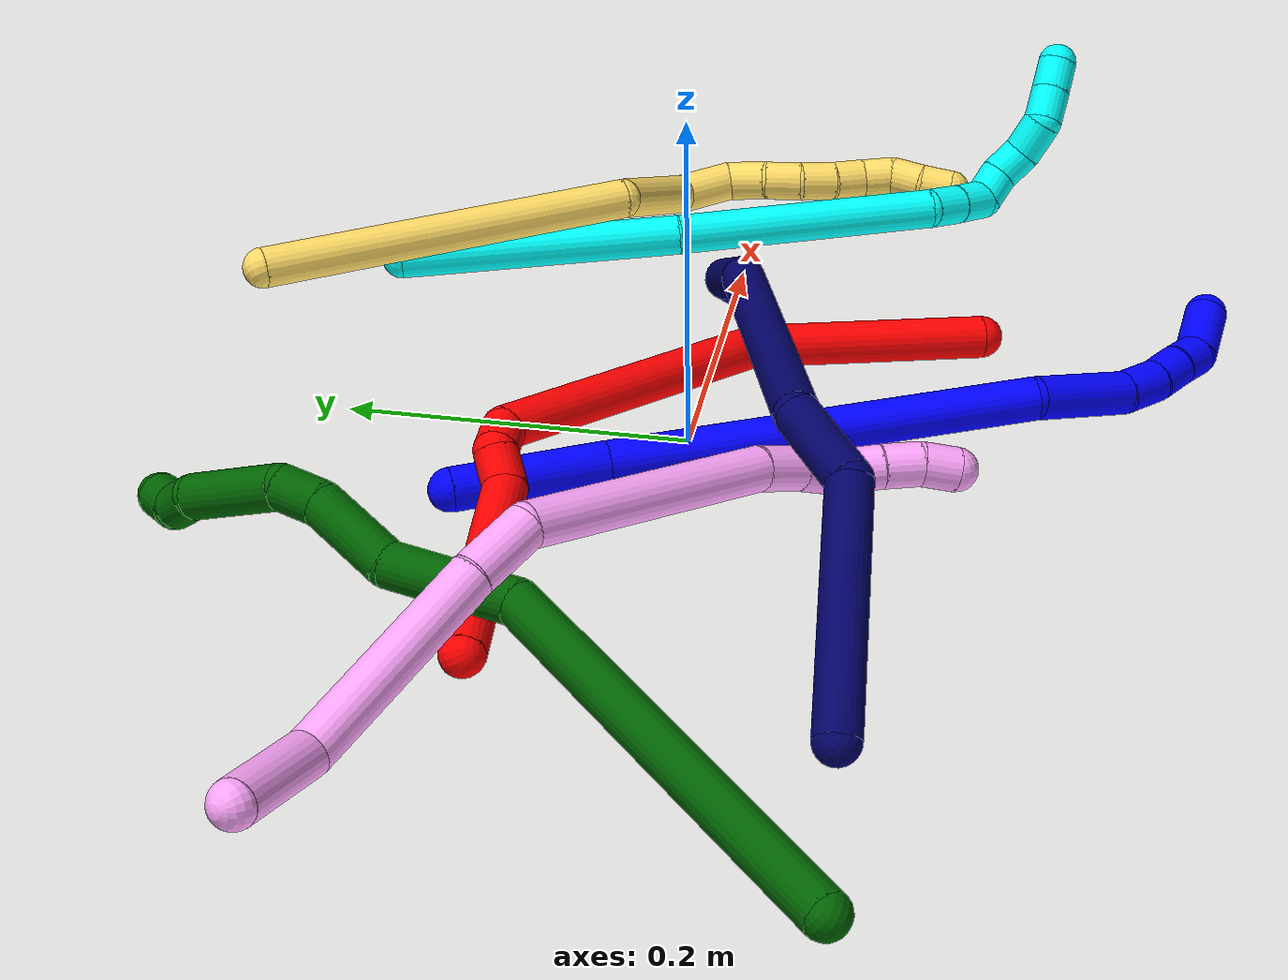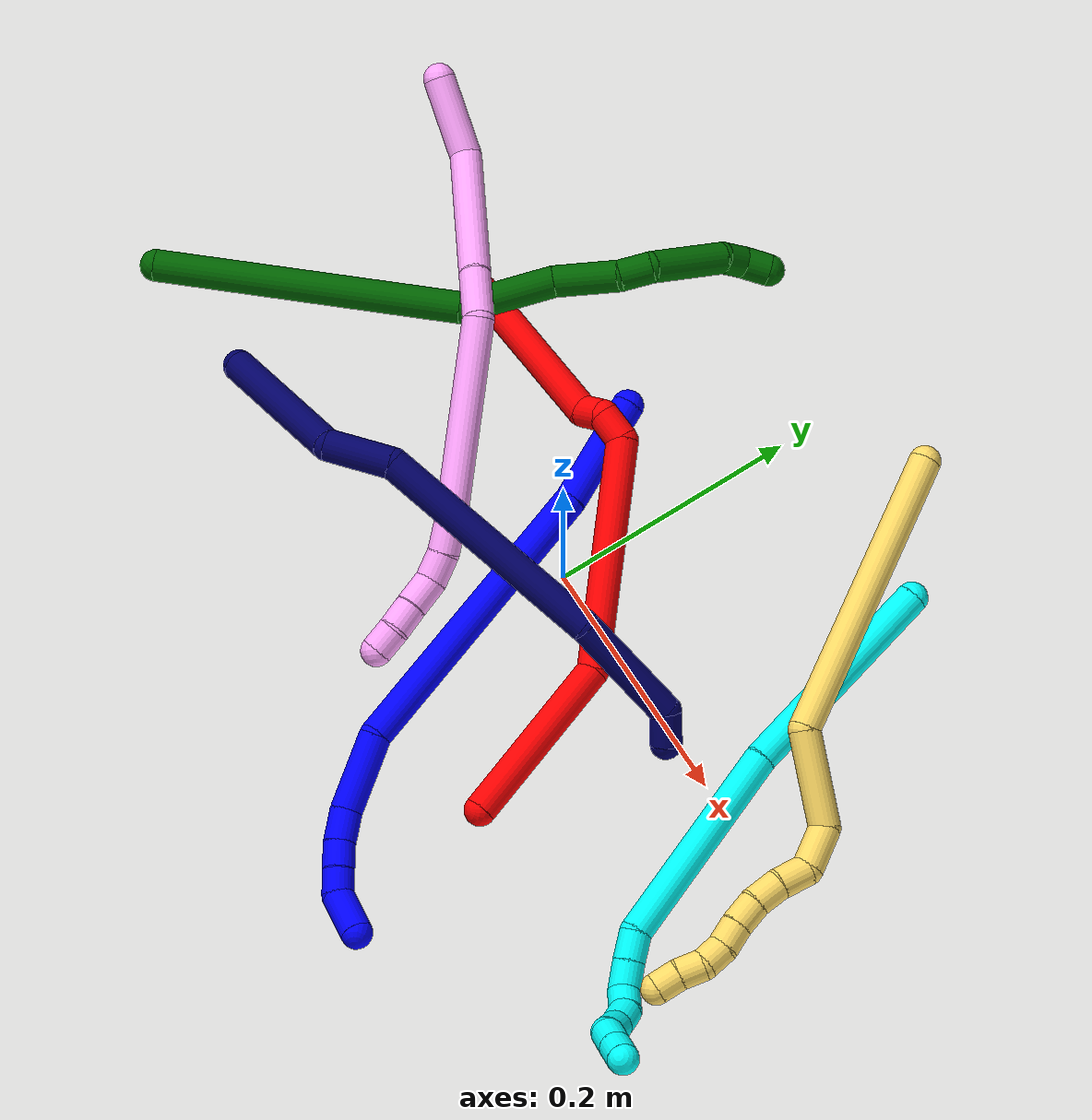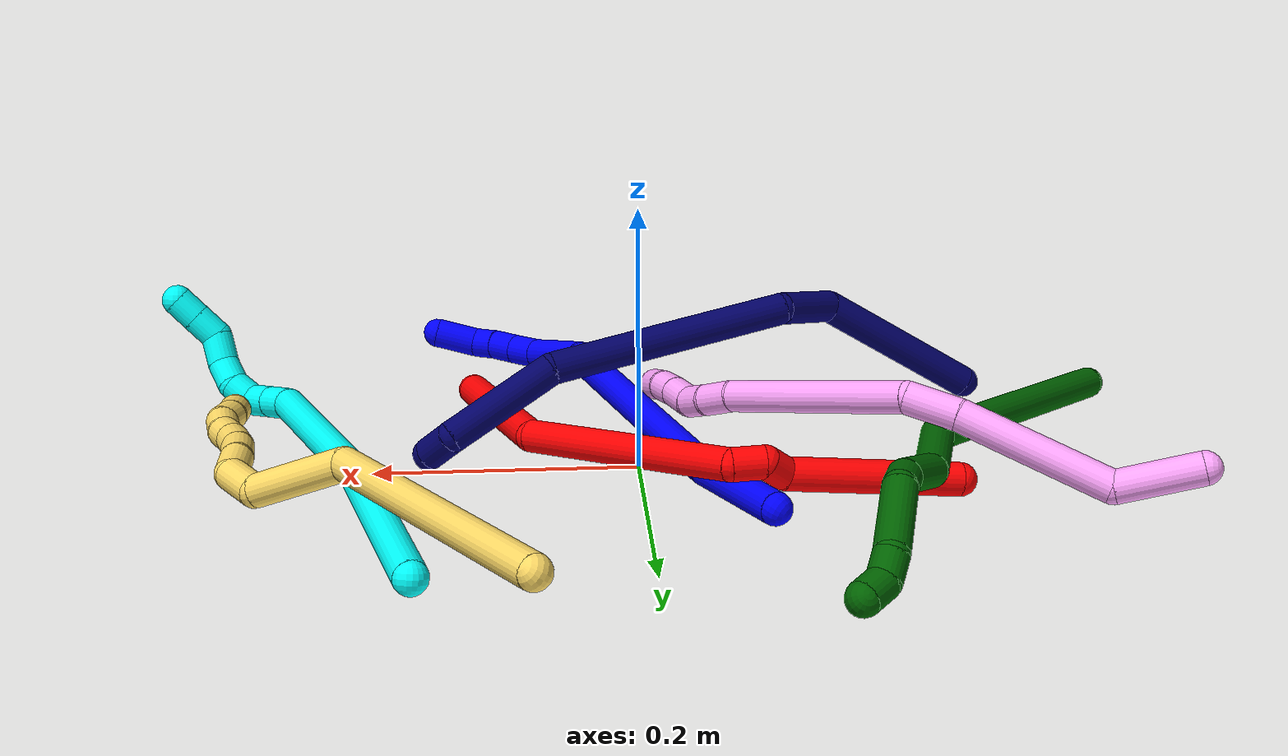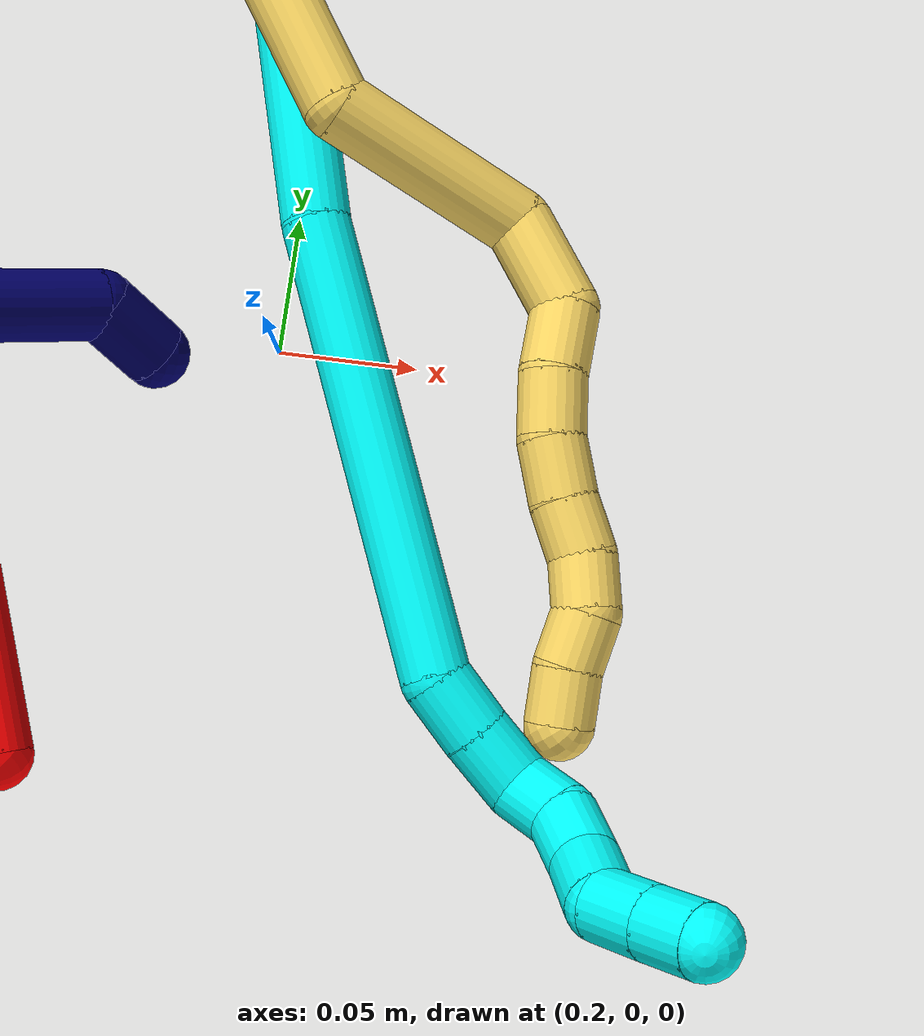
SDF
<sdf version="1.7">
 <world name="default">
  <plugin name="TubeGeneratorPlugin" filename="libtube_generator_plugin.so"/>
  <model name="photoneo_s_sensor">
   <static>1</static>
   <pose>0 0 2 1.57079 1.57079 3.14159</pose>
   <link name="link">
    <inertial><mass>0.1</mass></inertial>
    <sensor name="sensor" type="depth">
     <update_rate>30</update_rate>
     <camera>
      <horizontal_fov>1.22</horizontal_fov>
      <image><width>1920</width><height>1200</height><format>B8G8R8</format></image>
      <clip><near>0.1</near><far>4</far></clip>
      <depth_camera><output>points</output></depth_camera>
     </camera>
     <plugin name="camera_plugin" filename="libgazebo_ros_depth_camera.so">
      <baseline>0.2</baseline>
      <alwaysOn>1</alwaysOn>
      <updateRate>0.0</updateRate>
      <cameraName>camera_ir</cameraName>
      <imageTopicName>/camera/color/image_raw</imageTopicName>
      <cameraInfoTopicName>/camera/color/camera_info</cameraInfoTopicName>
      <depthImageTopicName>/camera/depth/image_raw</depthImageTopicName>
      <depthImageCameraInfoTopicName>/camera/depth/camera_info</depthImageCameraInfoTopicName>
      <pointCloudTopicName>/camera/depth/points</pointCloudTopicName>
      <frameName>fr_optical</frameName>
      <pointCloudCutoff>0.1</pointCloudCutoff>
      <pointCloudCutoffMax>2.0</pointCloudCutoffMax>
      <distortionK1>0</distortionK1>
      <distortionK2>0</distortionK2>
      <distortionK3>0</distortionK3>
      <distortionT1>0</distortionT1>
      <distortionT2>0</distortionT2>
      <CxPrime>0</CxPrime>
      <Cx>0</Cx>
      <Cy>0</Cy>
      <focalLength>0</focalLength>
      <hackBaseline>0</hackBaseline>
     </plugin>
    </sensor>
   </link>
  </model>
  <gravity>0 0 -9.8</gravity>
  <magnetic_field>6e-06 2.3e-05 -4.2e-05</magnetic_field>
  <atmosphere type="adiabatic"/>
  <physics name="default_physics" default="0" type="ode">
   <max_step_size>0.003</max_step_size>
   <real_time_factor>1</real_time_factor>
   <real_time_update_rate>1000</real_time_update_rate>
   <max_contacts>10000</max_contacts>
   <ode>
    <solver>
     <type>quick</type>
     <iters>100</iters>
     <sor>1.3</sor>
     <use_dynamic_moi_rescaling>0</use_dynamic_moi_rescaling>
    </solver>
    <constraints>
     <contact_max_correcting_vel>0</contact_max_correcting_vel>
     <contact_surface_layer>0.001</contact_surface_layer>
     <cfm>0</cfm>
     <erp>0.2</erp>
    </constraints>
   </ode>
  </physics>
  <scene><ambient>0.4 0.4 0.4 1</ambient><background>0.7 0.7 0.7 1</background><shadows>0</shadows></scene>
  <audio><device>default</device></audio>
  <spherical_coordinates>
   <surface_model>EARTH_WGS84</surface_model>
   <latitude_deg>0</latitude_deg>
   <longitude_deg>0</longitude_deg>
   <elevation>0</elevation>
   <heading_deg>0</heading_deg>
  </spherical_coordinates>
  <model name="bin">
   <static>1</static>
   <link name="bottom">
    <collision name="collision-bottom">
     <pose>0 0 -0.01 0 -0 0</pose>
     <geometry><box><size>0.8 0.6 0.02</size></box></geometry>
     <surface>
      <friction><ode><mu>100</mu><mu2>100</mu2></ode></friction>
      <contact><collide_bitmask>65535</collide_bitmask></contact>
     </surface>
    </collision>
   </link>
   <link name="west_wall">
    <collision name="collision-west_wall">
     <pose>-0.41 0 0.1 0 -0 0</pose>
     <geometry><box><size>0.02 0.6 0.2</size></box></geometry>
     <surface>
      <friction><ode><mu>100</mu><mu2>100</mu2></ode></friction>
      <contact><collide_bitmask>65535</collide_bitmask></contact>
     </surface>
    </collision>
   </link>
   <link name="east_wall">
    <collision name="collision-east_wall">
     <pose>0.41 0 0.1 0 -0 0</pose>
     <geometry><box><size>0.02 0.6 0.2</size></box></geometry>
     <surface>
      <friction><ode><mu>100</mu><mu2>100</mu2></ode></friction>
      <contact><collide_bitmask>65535</collide_bitmask></contact>
     </surface>
    </collision>
   </link>
   <link name="south_wall">
    <collision name="collision-south_wall">
     <pose>0 -0.31 0.1 0 -0 0</pose>
     <geometry><box><size>0.8 0.02 0.2</size></box></geometry>
     <surface>
      <friction><ode><mu>100</mu><mu2>100</mu2></ode></friction>
      <contact><collide_bitmask>65535</collide_bitmask></contact>
     </surface>
    </collision>
   </link>
   <link name="north_wall">
    <collision name="collision-north_wall">
     <pose>0 0.31 0.1 0 -0 0</pose>
     <geometry><box><size>0.8 0.02 0.2</size></box></geometry>
     <surface>
      <friction><ode><mu>100</mu><mu2>100</mu2></ode></friction>
      <contact><collide_bitmask>65535</collide_bitmask></contact>
     </surface>
    </collision>
   </link>
  </model>
  <model name="1">
   <static>0</static>
   <link name="1">
    <collision name="collision-cylinder-e_1_1_4">
     <pose>0.017603 -0.017178 0.037435 0.430205 0.403896 0.089404</pose>
     <geometry><cylinder><radius>0.0125</radius><length>0.089584</length></cylinder></geometry>
     <surface>
      <friction><ode><mu>1.16</mu><mu2>1.16</mu2><slip1>0</slip1><slip2>0</slip2></ode></friction>
      <contact><ode><kp>1e+06</kp><kd>1</kd><max_vel>0</max_vel><min_depth>0.001</min_depth></ode></contact>
     </surface>
    </collision>
    <visual name="visual-cylinder-e_1_1_4">
     <pose>0.017603 -0.017178 0.037435 0.430205 0.403896 0.089404</pose>
     <geometry><cylinder><radius>0.0125</radius><length>0.089584</length></cylinder></geometry>
     <material><ambient>0 0 1 1</ambient></material>
    </visual>
    <collision name="collision-cylinder-e_2_4_5">
     <pose>0.074973 -0.096499 0.172942 0.564796 0.329988 0.09655</pose>
     <geometry><cylinder><radius>0.0125</radius><length>0.245449</length></cylinder></geometry>
     <surface>
      <friction><ode><mu>1.16</mu><mu2>1.16</mu2><slip1>0</slip1><slip2>0</slip2></ode></friction>
      <contact><ode><kp>1e+06</kp><kd>1</kd><max_vel>0</max_vel><min_depth>0.001</min_depth></ode></contact>
     </surface>
    </collision>
    <visual name="visual-cylinder-e_2_4_5">
     <pose>0.074973 -0.096499 0.172942 0.564796 0.329988 0.09655</pose>
     <geometry><cylinder><radius>0.0125</radius><length>0.245449</length></cylinder></geometry>
     <material><ambient>0 0 1 1</ambient></material>
    </visual>
    <collision name="collision-cylinder-e_3_5_6">
     <pose>0.132431 -0.165372 0.295425 0.268982 0.609805 0.085116</pose>
     <geometry><cylinder><radius>0.0125</radius><length>0.06178</length></cylinder></geometry>
     <surface>
      <friction><ode><mu>1.16</mu><mu2>1.16</mu2><slip1>0</slip1><slip2>0</slip2></ode></friction>
      <contact><ode><kp>1e+06</kp><kd>1</kd><max_vel>0</max_vel><min_depth>0.001</min_depth></ode></contact>
     </surface>
    </collision>
    <visual name="visual-cylinder-e_3_5_6">
     <pose>0.132431 -0.165372 0.295425 0.268982 0.609805 0.085116</pose>
     <geometry><cylinder><radius>0.0125</radius><length>0.06178</length></cylinder></geometry>
     <material><ambient>0 0 1 1</ambient></material>
    </visual>
    <collision name="collision-cylinder-e_4_6_7">
     <pose>0.15564 -0.172902 0.331485 0.068675 0.441516 0.015418</pose>
     <geometry><cylinder><radius>0.0125</radius><length>0.025827</length></cylinder></geometry>
     <surface>
      <friction><ode><mu>1.16</mu><mu2>1.16</mu2><slip1>0</slip1><slip2>0</slip2></ode></friction>
      <contact><ode><kp>1e+06</kp><kd>1</kd><max_vel>0</max_vel><min_depth>0.001</min_depth></ode></contact>
     </surface>
    </collision>
    <visual name="visual-cylinder-e_4_6_7">
     <pose>0.15564 -0.172902 0.331485 0.068675 0.441516 0.015418</pose>
     <geometry><cylinder><radius>0.0125</radius><length>0.025827</length></cylinder></geometry>
     <material><ambient>0 0 1 1</ambient></material>
    </visual>
    <collision name="collision-cylinder-e_5_7_8">
     <pose>0.164638 -0.172757 0.35322 -0.093541 0.330804 -0.015626</pose>
     <geometry><cylinder><radius>0.0125</radius><length>0.021425</length></cylinder></geometry>
     <surface>
      <friction><ode><mu>1.16</mu><mu2>1.16</mu2><slip1>0</slip1><slip2>0</slip2></ode></friction>
      <contact><ode><kp>1e+06</kp><kd>1</kd><max_vel>0</max_vel><min_depth>0.001</min_depth></ode></contact>
     </surface>
    </collision>
    <visual name="visual-cylinder-e_5_7_8">
     <pose>0.164638 -0.172757 0.35322 -0.093541 0.330804 -0.015626</pose>
     <geometry><cylinder><radius>0.0125</radius><length>0.021425</length></cylinder></geometry>
     <material><ambient>0 0 1 1</ambient></material>
    </visual>
    <collision name="collision-cylinder-e_6_8_9">
     <pose>0.172284 -0.170591 0.372341 -0.134196 0.428783 -0.029261</pose>
     <geometry><cylinder><radius>0.0125</radius><length>0.020046</length></cylinder></geometry>
     <surface>
      <friction><ode><mu>1.16</mu><mu2>1.16</mu2><slip1>0</slip1><slip2>0</slip2></ode></friction>
      <contact><ode><kp>1e+06</kp><kd>1</kd><max_vel>0</max_vel><min_depth>0.001</min_depth></ode></contact>
     </surface>
    </collision>
    <visual name="visual-cylinder-e_6_8_9">
     <pose>0.172284 -0.170591 0.372341 -0.134196 0.428783 -0.029261</pose>
     <geometry><cylinder><radius>0.0125</radius><length>0.020046</length></cylinder></geometry>
     <material><ambient>0 0 1 1</ambient></material>
    </visual>
    <collision name="collision-cylinder-e_7_9_2">
     <pose>0.177261 -0.160811 0.397125 -0.497868 0.045145 -0.011478</pose>
     <geometry><cylinder><radius>0.0125</radius><length>0.035888</length></cylinder></geometry>
     <surface>
      <friction><ode><mu>1.16</mu><mu2>1.16</mu2><slip1>0</slip1><slip2>0</slip2></ode></friction>
      <contact><ode><kp>1e+06</kp><kd>1</kd><max_vel>0</max_vel><min_depth>0.001</min_depth></ode></contact>
     </surface>
    </collision>
    <visual name="visual-cylinder-e_7_9_2">
     <pose>0.177261 -0.160811 0.397125 -0.497868 0.045145 -0.011478</pose>
     <geometry><cylinder><radius>0.0125</radius><length>0.035888</length></cylinder></geometry>
     <material><ambient>0 0 1 1</ambient></material>
    </visual>
    <collision name="collision-sphere-2">
     <pose>0.178071 -0.15225 0.412875 0 -0 0</pose>
     <geometry><sphere><radius>0.0125</radius></sphere></geometry>
     <surface>
      <friction><ode><mu>1.16</mu><mu2>1.16</mu2><slip1>0</slip1><slip2>0</slip2></ode></friction>
      <contact><ode><kp>1e+06</kp><kd>1</kd><max_vel>0</max_vel><min_depth>0.001</min_depth></ode></contact>
     </surface>
    </collision>
    <visual name="visual-sphere-2">
     <pose>0.178071 -0.15225 0.412875 0 -0 0</pose>
     <geometry><sphere><radius>0.0125</radius></sphere></geometry>
     <material><ambient>0 0 1 1</ambient></material>
    </visual>
    <collision name="collision-sphere-9">
     <pose>0.176452 -0.169371 0.381375 0 -0 0</pose>
     <geometry><sphere><radius>0.0125</radius></sphere></geometry>
     <surface>
      <friction><ode><mu>1.16</mu><mu2>1.16</mu2><slip1>0</slip1><slip2>0</slip2></ode></friction>
      <contact><ode><kp>1e+06</kp><kd>1</kd><max_vel>0</max_vel><min_depth>0.001</min_depth></ode></contact>
     </surface>
    </collision>
    <visual name="visual-sphere-9">
     <pose>0.176452 -0.169371 0.381375 0 -0 0</pose>
     <geometry><sphere><radius>0.0125</radius></sphere></geometry>
     <material><ambient>0 0 1 1</ambient></material>
    </visual>
    <collision name="collision-sphere-4">
     <pose>0.035207 -0.034355 0.07487 0 -0 0</pose>
     <geometry><sphere><radius>0.0125</radius></sphere></geometry>
     <surface>
      <friction><ode><mu>1.16</mu><mu2>1.16</mu2><slip1>0</slip1><slip2>0</slip2></ode></friction>
      <contact><ode><kp>1e+06</kp><kd>1</kd><max_vel>0</max_vel><min_depth>0.001</min_depth></ode></contact>
     </surface>
    </collision>
    <visual name="visual-sphere-4">
     <pose>0.035207 -0.034355 0.07487 0 -0 0</pose>
     <geometry><sphere><radius>0.0125</radius></sphere></geometry>
     <material><ambient>0 0 1 1</ambient></material>
    </visual>
    <collision name="collision-sphere-1">
     <geometry><sphere><radius>0.0125</radius></sphere></geometry>
     <surface>
      <friction><ode><mu>1.16</mu><mu2>1.16</mu2><slip1>0</slip1><slip2>0</slip2></ode></friction>
      <contact><ode><kp>1e+06</kp><kd>1</kd><max_vel>0</max_vel><min_depth>0.001</min_depth></ode></contact>
     </surface>
    </collision>
    <visual name="visual-sphere-1">
     <geometry><sphere><radius>0.0125</radius></sphere></geometry>
     <material><ambient>0 0 1 1</ambient></material>
    </visual>
    <collision name="collision-sphere-8">
     <pose>0.168117 -0.171811 0.363308 0 -0 0</pose>
     <geometry><sphere><radius>0.0125</radius></sphere></geometry>
     <surface>
      <friction><ode><mu>1.16</mu><mu2>1.16</mu2><slip1>0</slip1><slip2>0</slip2></ode></friction>
      <contact><ode><kp>1e+06</kp><kd>1</kd><max_vel>0</max_vel><min_depth>0.001</min_depth></ode></contact>
     </surface>
    </collision>
    <visual name="visual-sphere-8">
     <pose>0.168117 -0.171811 0.363308 0 -0 0</pose>
     <geometry><sphere><radius>0.0125</radius></sphere></geometry>
     <material><ambient>0 0 1 1</ambient></material>
    </visual>
    <collision name="collision-sphere-5">
     <pose>0.11474 -0.158642 0.271014 0 -0 0</pose>
     <geometry><sphere><radius>0.0125</radius></sphere></geometry>
     <surface>
      <friction><ode><mu>1.16</mu><mu2>1.16</mu2><slip1>0</slip1><slip2>0</slip2></ode></friction>
      <contact><ode><kp>1e+06</kp><kd>1</kd><max_vel>0</max_vel><min_depth>0.001</min_depth></ode></contact>
     </surface>
    </collision>
    <visual name="visual-sphere-5">
     <pose>0.11474 -0.158642 0.271014 0 -0 0</pose>
     <geometry><sphere><radius>0.0125</radius></sphere></geometry>
     <material><ambient>0 0 1 1</ambient></material>
    </visual>
    <collision name="collision-sphere-6">
     <pose>0.150122 -0.172101 0.319837 0 -0 0</pose>
     <geometry><sphere><radius>0.0125</radius></sphere></geometry>
     <surface>
      <friction><ode><mu>1.16</mu><mu2>1.16</mu2><slip1>0</slip1><slip2>0</slip2></ode></friction>
      <contact><ode><kp>1e+06</kp><kd>1</kd><max_vel>0</max_vel><min_depth>0.001</min_depth></ode></contact>
     </surface>
    </collision>
    <visual name="visual-sphere-6">
     <pose>0.150122 -0.172101 0.319837 0 -0 0</pose>
     <geometry><sphere><radius>0.0125</radius></sphere></geometry>
     <material><ambient>0 0 1 1</ambient></material>
    </visual>
    <collision name="collision-sphere-7">
     <pose>0.161158 -0.173703 0.343132 0 -0 0</pose>
     <geometry><sphere><radius>0.0125</radius></sphere></geometry>
     <surface>
      <friction><ode><mu>1.16</mu><mu2>1.16</mu2><slip1>0</slip1><slip2>0</slip2></ode></friction>
      <contact><ode><kp>1e+06</kp><kd>1</kd><max_vel>0</max_vel><min_depth>0.001</min_depth></ode></contact>
     </surface>
    </collision>
    <visual name="visual-sphere-7">
     <pose>0.161158 -0.173703 0.343132 0 -0 0</pose>
     <geometry><sphere><radius>0.0125</radius></sphere></geometry>
     <material><ambient>0 0 1 1</ambient></material>
    </visual>
    <inertial>
     <pose>0.091046 -0.105598 0.203797 0 -0 0</pose>
     <mass>0.5</mass>
     <inertia>
      <ixx>0.00139</ixx>
      <ixy>0</ixy>
      <ixz>0</ixz>
      <iyy>0.001263</iyy>
      <iyz>0</iyz>
      <izz>0.000245</izz>
     </inertia>
    </inertial>
   </link>
   <pose>-0.08847 0.115918 0.011793 -0.30538 1.16746 -0.975531</pose>
  </model>
  <model name="2">
   <static>0</static>
   <link name="2">
    <collision name="collision-cylinder-e_1_1_4">
     <pose>-0.028809 0.045923 -0.043532 -2.32947 -0.427241 0.934547</pose>
     <geometry><cylinder><radius>0.0125</radius><length>0.139052</length></cylinder></geometry>
     <surface>
      <friction><ode><mu>1.16</mu><mu2>1.16</mu2><slip1>0</slip1><slip2>0</slip2></ode></friction>
      <contact><ode><kp>1e+06</kp><kd>1</kd><max_vel>0</max_vel><min_depth>0.001</min_depth></ode></contact>
     </surface>
    </collision>
    <visual name="visual-cylinder-e_1_1_4">
     <pose>-0.028809 0.045923 -0.043532 -2.32947 -0.427241 0.934547</pose>
     <geometry><cylinder><radius>0.0125</radius><length>0.139052</length></cylinder></geometry>
     <material><ambient>1 0 0 1</ambient></material>
    </visual>
    <collision name="collision-cylinder-e_2_4_5">
     <pose>-0.129409 0.14397 -0.110008 -1.98545 -0.900163 1.27487</pose>
     <geometry><cylinder><radius>0.0125</radius><length>0.183274</length></cylinder></geometry>
     <surface>
      <friction><ode><mu>1.16</mu><mu2>1.16</mu2><slip1>0</slip1><slip2>0</slip2></ode></friction>
      <contact><ode><kp>1e+06</kp><kd>1</kd><max_vel>0</max_vel><min_depth>0.001</min_depth></ode></contact>
     </surface>
    </collision>
    <visual name="visual-cylinder-e_2_4_5">
     <pose>-0.129409 0.14397 -0.110008 -1.98545 -0.900163 1.27487</pose>
     <geometry><cylinder><radius>0.0125</radius><length>0.183274</length></cylinder></geometry>
     <material><ambient>1 0 0 1</ambient></material>
    </visual>
    <collision name="collision-cylinder-e_3_5_6">
     <pose>-0.2129 0.197636 -0.129043 -0.375508 -1.22602 0.265708</pose>
     <geometry><cylinder><radius>0.0125</radius><length>0.024864</length></cylinder></geometry>
     <surface>
      <friction><ode><mu>1.16</mu><mu2>1.16</mu2><slip1>0</slip1><slip2>0</slip2></ode></friction>
      <contact><ode><kp>1e+06</kp><kd>1</kd><max_vel>0</max_vel><min_depth>0.001</min_depth></ode></contact>
     </surface>
    </collision>
    <visual name="visual-cylinder-e_3_5_6">
     <pose>-0.2129 0.197636 -0.129043 -0.375508 -1.22602 0.265708</pose>
     <geometry><cylinder><radius>0.0125</radius><length>0.024864</length></cylinder></geometry>
     <material><ambient>1 0 0 1</ambient></material>
    </visual>
    <collision name="collision-cylinder-e_4_6_7">
     <pose>-0.233132 0.192649 -0.123467 1.32087 -0.902369 -0.719947</pose>
     <geometry><cylinder><radius>0.0125</radius><length>0.021741</length></cylinder></geometry>
     <surface>
      <friction><ode><mu>1.16</mu><mu2>1.16</mu2><slip1>0</slip1><slip2>0</slip2></ode></friction>
      <contact><ode><kp>1e+06</kp><kd>1</kd><max_vel>0</max_vel><min_depth>0.001</min_depth></ode></contact>
     </surface>
    </collision>
    <visual name="visual-cylinder-e_4_6_7">
     <pose>-0.233132 0.192649 -0.123467 1.32087 -0.902369 -0.719947</pose>
     <geometry><cylinder><radius>0.0125</radius><length>0.021741</length></cylinder></geometry>
     <material><ambient>1 0 0 1</ambient></material>
    </visual>
    <collision name="collision-cylinder-e_5_7_2">
     <pose>-0.305032 0.1872 -0.105129 -0.064615 -1.31302 0.049794</pose>
     <geometry><cylinder><radius>0.0125</radius><length>0.131069</length></cylinder></geometry>
     <surface>
      <friction><ode><mu>1.16</mu><mu2>1.16</mu2><slip1>0</slip1><slip2>0</slip2></ode></friction>
      <contact><ode><kp>1e+06</kp><kd>1</kd><max_vel>0</max_vel><min_depth>0.001</min_depth></ode></contact>
     </surface>
    </collision>
    <visual name="visual-cylinder-e_5_7_2">
     <pose>-0.305032 0.1872 -0.105129 -0.064615 -1.31302 0.049794</pose>
     <geometry><cylinder><radius>0.0125</radius><length>0.131069</length></cylinder></geometry>
     <material><ambient>1 0 0 1</ambient></material>
    </visual>
    <collision name="collision-sphere-2">
     <pose>-0.368401 0.188279 -0.088457 0 -0 0</pose>
     <geometry><sphere><radius>0.0125</radius></sphere></geometry>
     <surface>
      <friction><ode><mu>1.16</mu><mu2>1.16</mu2><slip1>0</slip1><slip2>0</slip2></ode></friction>
      <contact><ode><kp>1e+06</kp><kd>1</kd><max_vel>0</max_vel><min_depth>0.001</min_depth></ode></contact>
     </surface>
    </collision>
    <visual name="visual-sphere-2">
     <pose>-0.368401 0.188279 -0.088457 0 -0 0</pose>
     <geometry><sphere><radius>0.0125</radius></sphere></geometry>
     <material><ambient>1 0 0 1</ambient></material>
    </visual>
    <collision name="collision-sphere-7">
     <pose>-0.241663 0.186121 -0.121801 0 -0 0</pose>
     <geometry><sphere><radius>0.0125</radius></sphere></geometry>
     <surface>
      <friction><ode><mu>1.16</mu><mu2>1.16</mu2><slip1>0</slip1><slip2>0</slip2></ode></friction>
      <contact><ode><kp>1e+06</kp><kd>1</kd><max_vel>0</max_vel><min_depth>0.001</min_depth></ode></contact>
     </surface>
    </collision>
    <visual name="visual-sphere-7">
     <pose>-0.241663 0.186121 -0.121801 0 -0 0</pose>
     <geometry><sphere><radius>0.0125</radius></sphere></geometry>
     <material><ambient>1 0 0 1</ambient></material>
    </visual>
    <collision name="collision-sphere-6">
     <pose>-0.2246 0.199177 -0.125133 0 -0 0</pose>
     <geometry><sphere><radius>0.0125</radius></sphere></geometry>
     <surface>
      <friction><ode><mu>1.16</mu><mu2>1.16</mu2><slip1>0</slip1><slip2>0</slip2></ode></friction>
      <contact><ode><kp>1e+06</kp><kd>1</kd><max_vel>0</max_vel><min_depth>0.001</min_depth></ode></contact>
     </surface>
    </collision>
    <visual name="visual-sphere-6">
     <pose>-0.2246 0.199177 -0.125133 0 -0 0</pose>
     <geometry><sphere><radius>0.0125</radius></sphere></geometry>
     <material><ambient>1 0 0 1</ambient></material>
    </visual>
    <collision name="collision-sphere-5">
     <pose>-0.2012 0.196095 -0.132952 0 -0 0</pose>
     <geometry><sphere><radius>0.0125</radius></sphere></geometry>
     <surface>
      <friction><ode><mu>1.16</mu><mu2>1.16</mu2><slip1>0</slip1><slip2>0</slip2></ode></friction>
      <contact><ode><kp>1e+06</kp><kd>1</kd><max_vel>0</max_vel><min_depth>0.001</min_depth></ode></contact>
     </surface>
    </collision>
    <visual name="visual-sphere-5">
     <pose>-0.2012 0.196095 -0.132952 0 -0 0</pose>
     <geometry><sphere><radius>0.0125</radius></sphere></geometry>
     <material><ambient>1 0 0 1</ambient></material>
    </visual>
    <collision name="collision-sphere-1">
     <geometry><sphere><radius>0.0125</radius></sphere></geometry>
     <surface>
      <friction><ode><mu>1.16</mu><mu2>1.16</mu2><slip1>0</slip1><slip2>0</slip2></ode></friction>
      <contact><ode><kp>1e+06</kp><kd>1</kd><max_vel>0</max_vel><min_depth>0.001</min_depth></ode></contact>
     </surface>
    </collision>
    <visual name="visual-sphere-1">
     <geometry><sphere><radius>0.0125</radius></sphere></geometry>
     <material><ambient>1 0 0 1</ambient></material>
    </visual>
    <collision name="collision-sphere-4">
     <pose>-0.057618 0.091846 -0.087064 0 -0 0</pose>
     <geometry><sphere><radius>0.0125</radius></sphere></geometry>
     <surface>
      <friction><ode><mu>1.16</mu><mu2>1.16</mu2><slip1>0</slip1><slip2>0</slip2></ode></friction>
      <contact><ode><kp>1e+06</kp><kd>1</kd><max_vel>0</max_vel><min_depth>0.001</min_depth></ode></contact>
     </surface>
    </collision>
    <visual name="visual-sphere-4">
     <pose>-0.057618 0.091846 -0.087064 0 -0 0</pose>
     <geometry><sphere><radius>0.0125</radius></sphere></geometry>
     <material><ambient>1 0 0 1</ambient></material>
    </visual>
    <inertial>
     <pose>-0.156131 0.13282 -0.091773 0 -0 0</pose>
     <mass>0.5</mass>
     <inertia>
      <ixx>0.000719</ixx>
      <ixy>0</ixy>
      <ixz>0</ixz>
      <iyy>0.000947</iyy>
      <iyz>0</iyz>
      <izz>0.000236</izz>
     </inertia>
    </inertial>
   </link>
   <pose>0.126096 -0.156366 0.011494 0.936374 -0.260729 -0.124419</pose>
  </model>
  <model name="3">
   <static>0</static>
   <link name="3">
    <collision name="collision-cylinder-e_1_1_4">
     <pose>-0.011075 -0.083696 -0.025681 1.86851 -0.125834 -0.170048</pose>
     <geometry><cylinder><radius>0.0125</radius><length>0.17649</length></cylinder></geometry>
     <surface>
      <friction><ode><mu>1.16</mu><mu2>1.16</mu2><slip1>0</slip1><slip2>0</slip2></ode></friction>
      <contact><ode><kp>1e+06</kp><kd>1</kd><max_vel>0</max_vel><min_depth>0.001</min_depth></ode></contact>
     </surface>
    </collision>
    <visual name="visual-cylinder-e_1_1_4">
     <pose>-0.011075 -0.083696 -0.025681 1.86851 -0.125834 -0.170048</pose>
     <geometry><cylinder><radius>0.0125</radius><length>0.17649</length></cylinder></geometry>
     <material><ambient>0.003922 1 0.996078 1</ambient></material>
    </visual>
    <collision name="collision-cylinder-e_2_4_5">
     <pose>-0.042117 -0.246324 -0.070623 1.81014 -0.24098 -0.305941</pose>
     <geometry><cylinder><radius>0.0125</radius><length>0.167331</length></cylinder></geometry>
     <surface>
      <friction><ode><mu>1.16</mu><mu2>1.16</mu2><slip1>0</slip1><slip2>0</slip2></ode></friction>
      <contact><ode><kp>1e+06</kp><kd>1</kd><max_vel>0</max_vel><min_depth>0.001</min_depth></ode></contact>
     </surface>
    </collision>
    <visual name="visual-cylinder-e_2_4_5">
     <pose>-0.042117 -0.246324 -0.070623 1.81014 -0.24098 -0.305941</pose>
     <geometry><cylinder><radius>0.0125</radius><length>0.167331</length></cylinder></geometry>
     <material><ambient>0.003922 1 0.996078 1</ambient></material>
    </visual>
    <collision name="collision-cylinder-e_3_5_6">
     <pose>-0.068505 -0.33488 -0.089919 1.57445 -0.58834 -0.590369</pose>
     <geometry><cylinder><radius>0.0125</radius><length>0.023138</length></cylinder></geometry>
     <surface>
      <friction><ode><mu>1.16</mu><mu2>1.16</mu2><slip1>0</slip1><slip2>0</slip2></ode></friction>
      <contact><ode><kp>1e+06</kp><kd>1</kd><max_vel>0</max_vel><min_depth>0.001</min_depth></ode></contact>
     </surface>
    </collision>
    <visual name="visual-cylinder-e_3_5_6">
     <pose>-0.068505 -0.33488 -0.089919 1.57445 -0.58834 -0.590369</pose>
     <geometry><cylinder><radius>0.0125</radius><length>0.023138</length></cylinder></geometry>
     <material><ambient>0.003922 1 0.996078 1</ambient></material>
    </visual>
    <collision name="collision-cylinder-e_4_6_7">
     <pose>-0.081947 -0.353864 -0.089969 1.57233 -0.643608 -0.644531</pose>
     <geometry><cylinder><radius>0.0125</radius><length>0.023402</length></cylinder></geometry>
     <surface>
      <friction><ode><mu>1.16</mu><mu2>1.16</mu2><slip1>0</slip1><slip2>0</slip2></ode></friction>
      <contact><ode><kp>1e+06</kp><kd>1</kd><max_vel>0</max_vel><min_depth>0.001</min_depth></ode></contact>
     </surface>
    </collision>
    <visual name="visual-cylinder-e_4_6_7">
     <pose>-0.081947 -0.353864 -0.089969 1.57233 -0.643608 -0.644531</pose>
     <geometry><cylinder><radius>0.0125</radius><length>0.023402</length></cylinder></geometry>
     <material><ambient>0.003922 1 0.996078 1</ambient></material>
    </visual>
    <collision name="collision-cylinder-e_5_7_8">
     <pose>-0.096776 -0.367329 -0.0959 2.53495 -0.825757 -1.90084</pose>
     <geometry><cylinder><radius>0.0125</radius><length>0.021243</length></cylinder></geometry>
     <surface>
      <friction><ode><mu>1.16</mu><mu2>1.16</mu2><slip1>0</slip1><slip2>0</slip2></ode></friction>
      <contact><ode><kp>1e+06</kp><kd>1</kd><max_vel>0</max_vel><min_depth>0.001</min_depth></ode></contact>
     </surface>
    </collision>
    <visual name="visual-cylinder-e_5_7_8">
     <pose>-0.096776 -0.367329 -0.0959 2.53495 -0.825757 -1.90084</pose>
     <geometry><cylinder><radius>0.0125</radius><length>0.021243</length></cylinder></geometry>
     <material><ambient>0.003922 1 0.996078 1</ambient></material>
    </visual>
    <collision name="collision-cylinder-e_6_8_9">
     <pose>-0.108587 -0.377188 -0.10984 2.51957 -0.38529 -1.09087</pose>
     <geometry><cylinder><radius>0.0125</radius><length>0.021308</length></cylinder></geometry>
     <surface>
      <friction><ode><mu>1.16</mu><mu2>1.16</mu2><slip1>0</slip1><slip2>0</slip2></ode></friction>
      <contact><ode><kp>1e+06</kp><kd>1</kd><max_vel>0</max_vel><min_depth>0.001</min_depth></ode></contact>
     </surface>
    </collision>
    <visual name="visual-cylinder-e_6_8_9">
     <pose>-0.108587 -0.377188 -0.10984 2.51957 -0.38529 -1.09087</pose>
     <geometry><cylinder><radius>0.0125</radius><length>0.021308</length></cylinder></geometry>
     <material><ambient>0.003922 1 0.996078 1</ambient></material>
    </visual>
    <collision name="collision-cylinder-e_7_9_10">
     <pose>-0.115701 -0.3863 -0.129122 2.85156 -0.258704 -1.4553</pose>
     <geometry><cylinder><radius>0.0125</radius><length>0.024307</length></cylinder></geometry>
     <surface>
      <friction><ode><mu>1.16</mu><mu2>1.16</mu2><slip1>0</slip1><slip2>0</slip2></ode></friction>
      <contact><ode><kp>1e+06</kp><kd>1</kd><max_vel>0</max_vel><min_depth>0.001</min_depth></ode></contact>
     </surface>
    </collision>
    <visual name="visual-cylinder-e_7_9_10">
     <pose>-0.115701 -0.3863 -0.129122 2.85156 -0.258704 -1.4553</pose>
     <geometry><cylinder><radius>0.0125</radius><length>0.024307</length></cylinder></geometry>
     <material><ambient>0.003922 1 0.996078 1</ambient></material>
    </visual>
    <collision name="collision-cylinder-e_8_10_11">
     <pose>-0.127123 -0.39053 -0.14762 3.02204 -0.850716 -2.8789</pose>
     <geometry><cylinder><radius>0.0125</radius><length>0.022116</length></cylinder></geometry>
     <surface>
      <friction><ode><mu>1.16</mu><mu2>1.16</mu2><slip1>0</slip1><slip2>0</slip2></ode></friction>
      <contact><ode><kp>1e+06</kp><kd>1</kd><max_vel>0</max_vel><min_depth>0.001</min_depth></ode></contact>
     </surface>
    </collision>
    <visual name="visual-cylinder-e_8_10_11">
     <pose>-0.127123 -0.39053 -0.14762 3.02204 -0.850716 -2.8789</pose>
     <geometry><cylinder><radius>0.0125</radius><length>0.022116</length></cylinder></geometry>
     <material><ambient>0.003922 1 0.996078 1</ambient></material>
    </visual>
    <collision name="collision-cylinder-e_9_11_2">
     <pose>-0.14318 -0.392043 -0.16167 3.04737 -0.84735 -2.93327</pose>
     <geometry><cylinder><radius>0.0125</radius><length>0.020665</length></cylinder></geometry>
     <surface>
      <friction><ode><mu>1.16</mu><mu2>1.16</mu2><slip1>0</slip1><slip2>0</slip2></ode></friction>
      <contact><ode><kp>1e+06</kp><kd>1</kd><max_vel>0</max_vel><min_depth>0.001</min_depth></ode></contact>
     </surface>
    </collision>
    <visual name="visual-cylinder-e_9_11_2">
     <pose>-0.14318 -0.392043 -0.16167 3.04737 -0.84735 -2.93327</pose>
     <geometry><cylinder><radius>0.0125</radius><length>0.020665</length></cylinder></geometry>
     <material><ambient>0.003922 1 0.996078 1</ambient></material>
    </visual>
    <collision name="collision-sphere-2">
     <pose>-0.150925 -0.392687 -0.168479 0 -0 0</pose>
     <geometry><sphere><radius>0.0125</radius></sphere></geometry>
     <surface>
      <friction><ode><mu>1.16</mu><mu2>1.16</mu2><slip1>0</slip1><slip2>0</slip2></ode></friction>
      <contact><ode><kp>1e+06</kp><kd>1</kd><max_vel>0</max_vel><min_depth>0.001</min_depth></ode></contact>
     </surface>
    </collision>
    <visual name="visual-sphere-2">
     <pose>-0.150925 -0.392687 -0.168479 0 -0 0</pose>
     <geometry><sphere><radius>0.0125</radius></sphere></geometry>
     <material><ambient>0.003922 1 0.996078 1</ambient></material>
    </visual>
    <collision name="collision-sphere-11">
     <pose>-0.135436 -0.3914 -0.15486 0 -0 0</pose>
     <geometry><sphere><radius>0.0125</radius></sphere></geometry>
     <surface>
      <friction><ode><mu>1.16</mu><mu2>1.16</mu2><slip1>0</slip1><slip2>0</slip2></ode></friction>
      <contact><ode><kp>1e+06</kp><kd>1</kd><max_vel>0</max_vel><min_depth>0.001</min_depth></ode></contact>
     </surface>
    </collision>
    <visual name="visual-sphere-11">
     <pose>-0.135436 -0.3914 -0.15486 0 -0 0</pose>
     <geometry><sphere><radius>0.0125</radius></sphere></geometry>
     <material><ambient>0.003922 1 0.996078 1</ambient></material>
    </visual>
    <collision name="collision-sphere-10">
     <pose>-0.11881 -0.38966 -0.14038 0 -0 0</pose>
     <geometry><sphere><radius>0.0125</radius></sphere></geometry>
     <surface>
      <friction><ode><mu>1.16</mu><mu2>1.16</mu2><slip1>0</slip1><slip2>0</slip2></ode></friction>
      <contact><ode><kp>1e+06</kp><kd>1</kd><max_vel>0</max_vel><min_depth>0.001</min_depth></ode></contact>
     </surface>
    </collision>
    <visual name="visual-sphere-10">
     <pose>-0.11881 -0.38966 -0.14038 0 -0 0</pose>
     <geometry><sphere><radius>0.0125</radius></sphere></geometry>
     <material><ambient>0.003922 1 0.996078 1</ambient></material>
    </visual>
    <collision name="collision-sphere-9">
     <pose>-0.112591 -0.38294 -0.117863 0 -0 0</pose>
     <geometry><sphere><radius>0.0125</radius></sphere></geometry>
     <surface>
      <friction><ode><mu>1.16</mu><mu2>1.16</mu2><slip1>0</slip1><slip2>0</slip2></ode></friction>
      <contact><ode><kp>1e+06</kp><kd>1</kd><max_vel>0</max_vel><min_depth>0.001</min_depth></ode></contact>
     </surface>
    </collision>
    <visual name="visual-sphere-9">
     <pose>-0.112591 -0.38294 -0.117863 0 -0 0</pose>
     <geometry><sphere><radius>0.0125</radius></sphere></geometry>
     <material><ambient>0.003922 1 0.996078 1</ambient></material>
    </visual>
    <collision name="collision-sphere-4">
     <pose>-0.02215 -0.167393 -0.051361 0 -0 0</pose>
     <geometry><sphere><radius>0.0125</radius></sphere></geometry>
     <surface>
      <friction><ode><mu>1.16</mu><mu2>1.16</mu2><slip1>0</slip1><slip2>0</slip2></ode></friction>
      <contact><ode><kp>1e+06</kp><kd>1</kd><max_vel>0</max_vel><min_depth>0.001</min_depth></ode></contact>
     </surface>
    </collision>
    <visual name="visual-sphere-4">
     <pose>-0.02215 -0.167393 -0.051361 0 -0 0</pose>
     <geometry><sphere><radius>0.0125</radius></sphere></geometry>
     <material><ambient>0.003922 1 0.996078 1</ambient></material>
    </visual>
    <collision name="collision-sphere-1">
     <geometry><sphere><radius>0.0125</radius></sphere></geometry>
     <surface>
      <friction><ode><mu>1.16</mu><mu2>1.16</mu2><slip1>0</slip1><slip2>0</slip2></ode></friction>
      <contact><ode><kp>1e+06</kp><kd>1</kd><max_vel>0</max_vel><min_depth>0.001</min_depth></ode></contact>
     </surface>
    </collision>
    <visual name="visual-sphere-1">
     <geometry><sphere><radius>0.0125</radius></sphere></geometry>
     <material><ambient>0.003922 1 0.996078 1</ambient></material>
    </visual>
    <collision name="collision-sphere-8">
     <pose>-0.104583 -0.371435 -0.101816 0 -0 0</pose>
     <geometry><sphere><radius>0.0125</radius></sphere></geometry>
     <surface>
      <friction><ode><mu>1.16</mu><mu2>1.16</mu2><slip1>0</slip1><slip2>0</slip2></ode></friction>
      <contact><ode><kp>1e+06</kp><kd>1</kd><max_vel>0</max_vel><min_depth>0.001</min_depth></ode></contact>
     </surface>
    </collision>
    <visual name="visual-sphere-8">
     <pose>-0.104583 -0.371435 -0.101816 0 -0 0</pose>
     <geometry><sphere><radius>0.0125</radius></sphere></geometry>
     <material><ambient>0.003922 1 0.996078 1</ambient></material>
    </visual>
    <collision name="collision-sphere-5">
     <pose>-0.062084 -0.325256 -0.089884 0 -0 0</pose>
     <geometry><sphere><radius>0.0125</radius></sphere></geometry>
     <surface>
      <friction><ode><mu>1.16</mu><mu2>1.16</mu2><slip1>0</slip1><slip2>0</slip2></ode></friction>
      <contact><ode><kp>1e+06</kp><kd>1</kd><max_vel>0</max_vel><min_depth>0.001</min_depth></ode></contact>
     </surface>
    </collision>
    <visual name="visual-sphere-5">
     <pose>-0.062084 -0.325256 -0.089884 0 -0 0</pose>
     <geometry><sphere><radius>0.0125</radius></sphere></geometry>
     <material><ambient>0.003922 1 0.996078 1</ambient></material>
    </visual>
    <collision name="collision-sphere-6">
     <pose>-0.074925 -0.344504 -0.089954 0 -0 0</pose>
     <geometry><sphere><radius>0.0125</radius></sphere></geometry>
     <surface>
      <friction><ode><mu>1.16</mu><mu2>1.16</mu2><slip1>0</slip1><slip2>0</slip2></ode></friction>
      <contact><ode><kp>1e+06</kp><kd>1</kd><max_vel>0</max_vel><min_depth>0.001</min_depth></ode></contact>
     </surface>
    </collision>
    <visual name="visual-sphere-6">
     <pose>-0.074925 -0.344504 -0.089954 0 -0 0</pose>
     <geometry><sphere><radius>0.0125</radius></sphere></geometry>
     <material><ambient>0.003922 1 0.996078 1</ambient></material>
    </visual>
    <collision name="collision-sphere-7">
     <pose>-0.088968 -0.363224 -0.089983 0 -0 0</pose>
     <geometry><sphere><radius>0.0125</radius></sphere></geometry>
     <surface>
      <friction><ode><mu>1.16</mu><mu2>1.16</mu2><slip1>0</slip1><slip2>0</slip2></ode></friction>
      <contact><ode><kp>1e+06</kp><kd>1</kd><max_vel>0</max_vel><min_depth>0.001</min_depth></ode></contact>
     </surface>
    </collision>
    <visual name="visual-sphere-7">
     <pose>-0.088968 -0.363224 -0.089983 0 -0 0</pose>
     <geometry><sphere><radius>0.0125</radius></sphere></geometry>
     <material><ambient>0.003922 1 0.996078 1</ambient></material>
    </visual>
    <inertial>
     <pose>-0.050914 -0.227975 -0.069315 0 -0 0</pose>
     <mass>0.5</mass>
     <inertia>
      <ixx>0.000611</ixx>
      <ixy>0</ixy>
      <ixz>0</ixz>
      <iyy>-0.000413</iyy>
      <iyz>0</iyz>
      <izz>0.000968</izz>
     </inertia>
    </inertial>
   </link>
   <pose>0.161416 0.213504 0.012047 2.87284 0.10674 -2.99123</pose>
  </model>
  <model name="4">
   <static>0</static>
   <link name="4">
    <collision name="collision-cylinder-e_1_1_4">
     <pose>-0.007444 0.000998 -0.031047 -3.10945 -0.235205 2.87119</pose>
     <geometry><cylinder><radius>0.0125</radius><length>0.063884</length></cylinder></geometry>
     <surface>
      <friction><ode><mu>1.16</mu><mu2>1.16</mu2><slip1>0</slip1><slip2>0</slip2></ode></friction>
      <contact><ode><kp>1e+06</kp><kd>1</kd><max_vel>0</max_vel><min_depth>0.001</min_depth></ode></contact>
     </surface>
    </collision>
    <visual name="visual-cylinder-e_1_1_4">
     <pose>-0.007444 0.000998 -0.031047 -3.10945 -0.235205 2.87119</pose>
     <geometry><cylinder><radius>0.0125</radius><length>0.063884</length></cylinder></geometry>
     <material><ambient>1 0.65098 0.996078 1</ambient></material>
    </visual>
    <collision name="collision-cylinder-e_2_4_5">
     <pose>-0.004634 0.033188 -0.1121 -2.58389 0.172257 -0.585794</pose>
     <geometry><cylinder><radius>0.0125</radius><length>0.119646</length></cylinder></geometry>
     <surface>
      <friction><ode><mu>1.16</mu><mu2>1.16</mu2><slip1>0</slip1><slip2>0</slip2></ode></friction>
      <contact><ode><kp>1e+06</kp><kd>1</kd><max_vel>0</max_vel><min_depth>0.001</min_depth></ode></contact>
     </surface>
    </collision>
    <visual name="visual-cylinder-e_2_4_5">
     <pose>-0.004634 0.033188 -0.1121 -2.58389 0.172257 -0.585794</pose>
     <geometry><cylinder><radius>0.0125</radius><length>0.119646</length></cylinder></geometry>
     <material><ambient>1 0.65098 0.996078 1</ambient></material>
    </visual>
    <collision name="collision-cylinder-e_3_5_6">
     <pose>0.008488 0.07293 -0.180318 -2.70263 0.141612 -0.615669</pose>
     <geometry><cylinder><radius>0.0125</radius><length>0.040643</length></cylinder></geometry>
     <surface>
      <friction><ode><mu>1.16</mu><mu2>1.16</mu2><slip1>0</slip1><slip2>0</slip2></ode></friction>
      <contact><ode><kp>1e+06</kp><kd>1</kd><max_vel>0</max_vel><min_depth>0.001</min_depth></ode></contact>
     </surface>
    </collision>
    <visual name="visual-cylinder-e_3_5_6">
     <pose>0.008488 0.07293 -0.180318 -2.70263 0.141612 -0.615669</pose>
     <geometry><cylinder><radius>0.0125</radius><length>0.040643</length></cylinder></geometry>
     <material><ambient>1 0.65098 0.996078 1</ambient></material>
    </visual>
    <collision name="collision-cylinder-e_4_6_7">
     <pose>0.029701 0.081415 -0.273951 3.14073 0.238591 3.13437</pose>
     <geometry><cylinder><radius>0.0125</radius><length>0.155241</length></cylinder></geometry>
     <surface>
      <friction><ode><mu>1.16</mu><mu2>1.16</mu2><slip1>0</slip1><slip2>0</slip2></ode></friction>
      <contact><ode><kp>1e+06</kp><kd>1</kd><max_vel>0</max_vel><min_depth>0.001</min_depth></ode></contact>
     </surface>
    </collision>
    <visual name="visual-cylinder-e_4_6_7">
     <pose>0.029701 0.081415 -0.273951 3.14073 0.238591 3.13437</pose>
     <geometry><cylinder><radius>0.0125</radius><length>0.155241</length></cylinder></geometry>
     <material><ambient>1 0.65098 0.996078 1</ambient></material>
    </visual>
    <collision name="collision-cylinder-e_5_7_8">
     <pose>0.051938 0.078909 -0.362791 2.96164 0.278026 1.99617</pose>
     <geometry><cylinder><radius>0.0125</radius><length>0.028367</length></cylinder></geometry>
     <surface>
      <friction><ode><mu>1.16</mu><mu2>1.16</mu2><slip1>0</slip1><slip2>0</slip2></ode></friction>
      <contact><ode><kp>1e+06</kp><kd>1</kd><max_vel>0</max_vel><min_depth>0.001</min_depth></ode></contact>
     </surface>
    </collision>
    <visual name="visual-cylinder-e_5_7_8">
     <pose>0.051938 0.078909 -0.362791 2.96164 0.278026 1.99617</pose>
     <geometry><cylinder><radius>0.0125</radius><length>0.028367</length></cylinder></geometry>
     <material><ambient>1 0.65098 0.996078 1</ambient></material>
    </visual>
    <collision name="collision-cylinder-e_6_8_9">
     <pose>0.061077 0.073676 -0.386274 2.87098 0.465499 2.09897</pose>
     <geometry><cylinder><radius>0.0125</radius><length>0.023376</length></cylinder></geometry>
     <surface>
      <friction><ode><mu>1.16</mu><mu2>1.16</mu2><slip1>0</slip1><slip2>0</slip2></ode></friction>
      <contact><ode><kp>1e+06</kp><kd>1</kd><max_vel>0</max_vel><min_depth>0.001</min_depth></ode></contact>
     </surface>
    </collision>
    <visual name="visual-cylinder-e_6_8_9">
     <pose>0.061077 0.073676 -0.386274 2.87098 0.465499 2.09897</pose>
     <geometry><cylinder><radius>0.0125</radius><length>0.023376</length></cylinder></geometry>
     <material><ambient>1 0.65098 0.996078 1</ambient></material>
    </visual>
    <collision name="collision-cylinder-e_7_9_10">
     <pose>0.07529 0.071174 -0.405593 -3.11026 0.769293 -3.06423</pose>
     <geometry><cylinder><radius>0.0125</radius><length>0.025778</length></cylinder></geometry>
     <surface>
      <friction><ode><mu>1.16</mu><mu2>1.16</mu2><slip1>0</slip1><slip2>0</slip2></ode></friction>
      <contact><ode><kp>1e+06</kp><kd>1</kd><max_vel>0</max_vel><min_depth>0.001</min_depth></ode></contact>
     </surface>
    </collision>
    <visual name="visual-cylinder-e_7_9_10">
     <pose>0.07529 0.071174 -0.405593 -3.11026 0.769293 -3.06423</pose>
     <geometry><cylinder><radius>0.0125</radius><length>0.025778</length></cylinder></geometry>
     <material><ambient>1 0.65098 0.996078 1</ambient></material>
    </visual>
    <collision name="collision-cylinder-e_8_10_11">
     <pose>0.091697 0.071079 -0.423105 3.09498 0.732957 3.02027</pose>
     <geometry><cylinder><radius>0.0125</radius><length>0.022245</length></cylinder></geometry>
     <surface>
      <friction><ode><mu>1.16</mu><mu2>1.16</mu2><slip1>0</slip1><slip2>0</slip2></ode></friction>
      <contact><ode><kp>1e+06</kp><kd>1</kd><max_vel>0</max_vel><min_depth>0.001</min_depth></ode></contact>
     </surface>
    </collision>
    <visual name="visual-cylinder-e_8_10_11">
     <pose>0.091697 0.071079 -0.423105 3.09498 0.732957 3.02027</pose>
     <geometry><cylinder><radius>0.0125</radius><length>0.022245</length></cylinder></geometry>
     <material><ambient>1 0.65098 0.996078 1</ambient></material>
    </visual>
    <collision name="collision-cylinder-e_9_11_2">
     <pose>0.106086 0.06811 -0.438672 2.80189 0.730662 2.2986</pose>
     <geometry><cylinder><radius>0.0125</radius><length>0.02082</length></cylinder></geometry>
     <surface>
      <friction><ode><mu>1.16</mu><mu2>1.16</mu2><slip1>0</slip1><slip2>0</slip2></ode></friction>
      <contact><ode><kp>1e+06</kp><kd>1</kd><max_vel>0</max_vel><min_depth>0.001</min_depth></ode></contact>
     </surface>
    </collision>
    <visual name="visual-cylinder-e_9_11_2">
     <pose>0.106086 0.06811 -0.438672 2.80189 0.730662 2.2986</pose>
     <geometry><cylinder><radius>0.0125</radius><length>0.02082</length></cylinder></geometry>
     <material><ambient>1 0.65098 0.996078 1</ambient></material>
    </visual>
    <collision name="collision-sphere-2">
     <pose>0.113033 0.065527 -0.445982 0 -0 0</pose>
     <geometry><sphere><radius>0.0125</radius></sphere></geometry>
     <surface>
      <friction><ode><mu>1.16</mu><mu2>1.16</mu2><slip1>0</slip1><slip2>0</slip2></ode></friction>
      <contact><ode><kp>1e+06</kp><kd>1</kd><max_vel>0</max_vel><min_depth>0.001</min_depth></ode></contact>
     </surface>
    </collision>
    <visual name="visual-sphere-2">
     <pose>0.113033 0.065527 -0.445982 0 -0 0</pose>
     <geometry><sphere><radius>0.0125</radius></sphere></geometry>
     <material><ambient>1 0.65098 0.996078 1</ambient></material>
    </visual>
    <collision name="collision-sphere-11">
     <pose>0.099139 0.070694 -0.431363 0 -0 0</pose>
     <geometry><sphere><radius>0.0125</radius></sphere></geometry>
     <surface>
      <friction><ode><mu>1.16</mu><mu2>1.16</mu2><slip1>0</slip1><slip2>0</slip2></ode></friction>
      <contact><ode><kp>1e+06</kp><kd>1</kd><max_vel>0</max_vel><min_depth>0.001</min_depth></ode></contact>
     </surface>
    </collision>
    <visual name="visual-sphere-11">
     <pose>0.099139 0.070694 -0.431363 0 -0 0</pose>
     <geometry><sphere><radius>0.0125</radius></sphere></geometry>
     <material><ambient>1 0.65098 0.996078 1</ambient></material>
    </visual>
    <collision name="collision-sphere-10">
     <pose>0.084256 0.071464 -0.414848 0 -0 0</pose>
     <geometry><sphere><radius>0.0125</radius></sphere></geometry>
     <surface>
      <friction><ode><mu>1.16</mu><mu2>1.16</mu2><slip1>0</slip1><slip2>0</slip2></ode></friction>
      <contact><ode><kp>1e+06</kp><kd>1</kd><max_vel>0</max_vel><min_depth>0.001</min_depth></ode></contact>
     </surface>
    </collision>
    <visual name="visual-sphere-10">
     <pose>0.084256 0.071464 -0.414848 0 -0 0</pose>
     <geometry><sphere><radius>0.0125</radius></sphere></geometry>
     <material><ambient>1 0.65098 0.996078 1</ambient></material>
    </visual>
    <collision name="collision-sphere-9">
     <pose>0.066324 0.070884 -0.396338 0 -0 0</pose>
     <geometry><sphere><radius>0.0125</radius></sphere></geometry>
     <surface>
      <friction><ode><mu>1.16</mu><mu2>1.16</mu2><slip1>0</slip1><slip2>0</slip2></ode></friction>
      <contact><ode><kp>1e+06</kp><kd>1</kd><max_vel>0</max_vel><min_depth>0.001</min_depth></ode></contact>
     </surface>
    </collision>
    <visual name="visual-sphere-9">
     <pose>0.066324 0.070884 -0.396338 0 -0 0</pose>
     <geometry><sphere><radius>0.0125</radius></sphere></geometry>
     <material><ambient>1 0.65098 0.996078 1</ambient></material>
    </visual>
    <collision name="collision-sphere-4">
     <pose>-0.014888 0.001996 -0.062093 0 -0 0</pose>
     <geometry><sphere><radius>0.0125</radius></sphere></geometry>
     <surface>
      <friction><ode><mu>1.16</mu><mu2>1.16</mu2><slip1>0</slip1><slip2>0</slip2></ode></friction>
      <contact><ode><kp>1e+06</kp><kd>1</kd><max_vel>0</max_vel><min_depth>0.001</min_depth></ode></contact>
     </surface>
    </collision>
    <visual name="visual-sphere-4">
     <pose>-0.014888 0.001996 -0.062093 0 -0 0</pose>
     <geometry><sphere><radius>0.0125</radius></sphere></geometry>
     <material><ambient>1 0.65098 0.996078 1</ambient></material>
    </visual>
    <collision name="collision-sphere-1">
     <geometry><sphere><radius>0.0125</radius></sphere></geometry>
     <surface>
      <friction><ode><mu>1.16</mu><mu2>1.16</mu2><slip1>0</slip1><slip2>0</slip2></ode></friction>
      <contact><ode><kp>1e+06</kp><kd>1</kd><max_vel>0</max_vel><min_depth>0.001</min_depth></ode></contact>
     </surface>
    </collision>
    <visual name="visual-sphere-1">
     <geometry><sphere><radius>0.0125</radius></sphere></geometry>
     <material><ambient>1 0.65098 0.996078 1</ambient></material>
    </visual>
    <collision name="collision-sphere-8">
     <pose>0.055831 0.076468 -0.37621 0 -0 0</pose>
     <geometry><sphere><radius>0.0125</radius></sphere></geometry>
     <surface>
      <friction><ode><mu>1.16</mu><mu2>1.16</mu2><slip1>0</slip1><slip2>0</slip2></ode></friction>
      <contact><ode><kp>1e+06</kp><kd>1</kd><max_vel>0</max_vel><min_depth>0.001</min_depth></ode></contact>
     </surface>
    </collision>
    <visual name="visual-sphere-8">
     <pose>0.055831 0.076468 -0.37621 0 -0 0</pose>
     <geometry><sphere><radius>0.0125</radius></sphere></geometry>
     <material><ambient>1 0.65098 0.996078 1</ambient></material>
    </visual>
    <collision name="collision-sphere-5">
     <pose>0.00562 0.06438 -0.162108 0 -0 0</pose>
     <geometry><sphere><radius>0.0125</radius></sphere></geometry>
     <surface>
      <friction><ode><mu>1.16</mu><mu2>1.16</mu2><slip1>0</slip1><slip2>0</slip2></ode></friction>
      <contact><ode><kp>1e+06</kp><kd>1</kd><max_vel>0</max_vel><min_depth>0.001</min_depth></ode></contact>
     </surface>
    </collision>
    <visual name="visual-sphere-5">
     <pose>0.00562 0.06438 -0.162108 0 -0 0</pose>
     <geometry><sphere><radius>0.0125</radius></sphere></geometry>
     <material><ambient>1 0.65098 0.996078 1</ambient></material>
    </visual>
    <collision name="collision-sphere-6">
     <pose>0.011357 0.08148 -0.198529 0 -0 0</pose>
     <geometry><sphere><radius>0.0125</radius></sphere></geometry>
     <surface>
      <friction><ode><mu>1.16</mu><mu2>1.16</mu2><slip1>0</slip1><slip2>0</slip2></ode></friction>
      <contact><ode><kp>1e+06</kp><kd>1</kd><max_vel>0</max_vel><min_depth>0.001</min_depth></ode></contact>
     </surface>
    </collision>
    <visual name="visual-sphere-6">
     <pose>0.011357 0.08148 -0.198529 0 -0 0</pose>
     <geometry><sphere><radius>0.0125</radius></sphere></geometry>
     <material><ambient>1 0.65098 0.996078 1</ambient></material>
    </visual>
    <collision name="collision-sphere-7">
     <pose>0.048045 0.08135 -0.349373 0 -0 0</pose>
     <geometry><sphere><radius>0.0125</radius></sphere></geometry>
     <surface>
      <friction><ode><mu>1.16</mu><mu2>1.16</mu2><slip1>0</slip1><slip2>0</slip2></ode></friction>
      <contact><ode><kp>1e+06</kp><kd>1</kd><max_vel>0</max_vel><min_depth>0.001</min_depth></ode></contact>
     </surface>
    </collision>
    <visual name="visual-sphere-7">
     <pose>0.048045 0.08135 -0.349373 0 -0 0</pose>
     <geometry><sphere><radius>0.0125</radius></sphere></geometry>
     <material><ambient>1 0.65098 0.996078 1</ambient></material>
    </visual>
    <inertial>
     <pose>0.026032 0.056864 -0.227148 0 -0 0</pose>
     <mass>0.5</mass>
     <inertia>
      <ixx>-0.000273</ixx>
      <ixy>0</ixy>
      <ixz>0</ixz>
      <iyy>0.000182</iyy>
      <iyz>0</iyz>
      <izz>-0.000215</izz>
     </inertia>
    </inertial>
   </link>
   <pose>-0.387559 0.133966 0.040724 1.29678 -0.254619 -1.9713</pose>
  </model>
  <model name="5">
   <static>0</static>
   <link name="5">
    <collision name="collision-cylinder-e_1_1_4">
     <pose>0.056792 -0.103099 0.001133 1.5598 0.503472 0.498194</pose>
     <geometry><cylinder><radius>0.0125</radius><length>0.235423</length></cylinder></geometry>
     <surface>
      <friction><ode><mu>1.16</mu><mu2>1.16</mu2><slip1>0</slip1><slip2>0</slip2></ode></friction>
      <contact><ode><kp>1e+06</kp><kd>1</kd><max_vel>0</max_vel><min_depth>0.001</min_depth></ode></contact>
     </surface>
    </collision>
    <visual name="visual-cylinder-e_1_1_4">
     <pose>0.056792 -0.103099 0.001133 1.5598 0.503472 0.498194</pose>
     <geometry><cylinder><radius>0.0125</radius><length>0.235423</length></cylinder></geometry>
     <material><ambient>1 0.858824 0.4 1</ambient></material>
    </visual>
    <collision name="collision-cylinder-e_2_4_5">
     <pose>0.106328 -0.243225 -0.005153 1.76857 -0.189854 -0.231334</pose>
     <geometry><cylinder><radius>0.0125</radius><length>0.076908</length></cylinder></geometry>
     <surface>
      <friction><ode><mu>1.16</mu><mu2>1.16</mu2><slip1>0</slip1><slip2>0</slip2></ode></friction>
      <contact><ode><kp>1e+06</kp><kd>1</kd><max_vel>0</max_vel><min_depth>0.001</min_depth></ode></contact>
     </surface>
    </collision>
    <visual name="visual-cylinder-e_2_4_5">
     <pose>0.106328 -0.243225 -0.005153 1.76857 -0.189854 -0.231334</pose>
     <geometry><cylinder><radius>0.0125</radius><length>0.076908</length></cylinder></geometry>
     <material><ambient>1 0.858824 0.4 1</ambient></material>
    </visual>
    <collision name="collision-cylinder-e_3_5_6">
     <pose>0.108406 -0.295795 -0.013494 1.62997 0.54011 0.571335</pose>
     <geometry><cylinder><radius>0.0125</radius><length>0.036309</length></cylinder></geometry>
     <surface>
      <friction><ode><mu>1.16</mu><mu2>1.16</mu2><slip1>0</slip1><slip2>0</slip2></ode></friction>
      <contact><ode><kp>1e+06</kp><kd>1</kd><max_vel>0</max_vel><min_depth>0.001</min_depth></ode></contact>
     </surface>
    </collision>
    <visual name="visual-cylinder-e_3_5_6">
     <pose>0.108406 -0.295795 -0.013494 1.62997 0.54011 0.571335</pose>
     <geometry><cylinder><radius>0.0125</radius><length>0.036309</length></cylinder></geometry>
     <material><ambient>1 0.858824 0.4 1</ambient></material>
    </visual>
    <collision name="collision-cylinder-e_4_6_7">
     <pose>0.127651 -0.317216 -0.009565 0.881034 0.915239 0.456246</pose>
     <geometry><cylinder><radius>0.0125</radius><length>0.025001</length></cylinder></geometry>
     <surface>
      <friction><ode><mu>1.16</mu><mu2>1.16</mu2><slip1>0</slip1><slip2>0</slip2></ode></friction>
      <contact><ode><kp>1e+06</kp><kd>1</kd><max_vel>0</max_vel><min_depth>0.001</min_depth></ode></contact>
     </surface>
    </collision>
    <visual name="visual-cylinder-e_4_6_7">
     <pose>0.127651 -0.317216 -0.009565 0.881034 0.915239 0.456246</pose>
     <geometry><cylinder><radius>0.0125</radius><length>0.025001</length></cylinder></geometry>
     <material><ambient>1 0.858824 0.4 1</ambient></material>
    </visual>
    <collision name="collision-cylinder-e_5_7_8">
     <pose>0.14549 -0.330426 -0.000429 1.04167 0.751072 0.444849</pose>
     <geometry><cylinder><radius>0.0125</radius><length>0.023239</length></cylinder></geometry>
     <surface>
      <friction><ode><mu>1.16</mu><mu2>1.16</mu2><slip1>0</slip1><slip2>0</slip2></ode></friction>
      <contact><ode><kp>1e+06</kp><kd>1</kd><max_vel>0</max_vel><min_depth>0.001</min_depth></ode></contact>
     </surface>
    </collision>
    <visual name="visual-cylinder-e_5_7_8">
     <pose>0.14549 -0.330426 -0.000429 1.04167 0.751072 0.444849</pose>
     <geometry><cylinder><radius>0.0125</radius><length>0.023239</length></cylinder></geometry>
     <material><ambient>1 0.858824 0.4 1</ambient></material>
    </visual>
    <collision name="collision-cylinder-e_6_8_9">
     <pose>0.159863 -0.346524 0.006579 1.26989 0.612168 0.457476</pose>
     <geometry><cylinder><radius>0.0125</radius><length>0.022429</length></cylinder></geometry>
     <surface>
      <friction><ode><mu>1.16</mu><mu2>1.16</mu2><slip1>0</slip1><slip2>0</slip2></ode></friction>
      <contact><ode><kp>1e+06</kp><kd>1</kd><max_vel>0</max_vel><min_depth>0.001</min_depth></ode></contact>
     </surface>
    </collision>
    <visual name="visual-cylinder-e_6_8_9">
     <pose>0.159863 -0.346524 0.006579 1.26989 0.612168 0.457476</pose>
     <geometry><cylinder><radius>0.0125</radius><length>0.022429</length></cylinder></geometry>
     <material><ambient>1 0.858824 0.4 1</ambient></material>
    </visual>
    <collision name="collision-cylinder-e_7_9_10">
     <pose>0.171754 -0.363934 0.010688 1.41151 0.556481 0.477559</pose>
     <geometry><cylinder><radius>0.0125</radius><length>0.020624</length></cylinder></geometry>
     <surface>
      <friction><ode><mu>1.16</mu><mu2>1.16</mu2><slip1>0</slip1><slip2>0</slip2></ode></friction>
      <contact><ode><kp>1e+06</kp><kd>1</kd><max_vel>0</max_vel><min_depth>0.001</min_depth></ode></contact>
     </surface>
    </collision>
    <visual name="visual-cylinder-e_7_9_10">
     <pose>0.171754 -0.363934 0.010688 1.41151 0.556481 0.477559</pose>
     <geometry><cylinder><radius>0.0125</radius><length>0.020624</length></cylinder></geometry>
     <material><ambient>1 0.858824 0.4 1</ambient></material>
    </visual>
    <collision name="collision-cylinder-e_8_10_11">
     <pose>0.184271 -0.379179 0.014628 1.20193 0.784989 0.553063</pose>
     <geometry><cylinder><radius>0.0125</radius><length>0.020004</length></cylinder></geometry>
     <surface>
      <friction><ode><mu>1.16</mu><mu2>1.16</mu2><slip1>0</slip1><slip2>0</slip2></ode></friction>
      <contact><ode><kp>1e+06</kp><kd>1</kd><max_vel>0</max_vel><min_depth>0.001</min_depth></ode></contact>
     </surface>
    </collision>
    <visual name="visual-cylinder-e_8_10_11">
     <pose>0.184271 -0.379179 0.014628 1.20193 0.784989 0.553063</pose>
     <geometry><cylinder><radius>0.0125</radius><length>0.020004</length></cylinder></geometry>
     <material><ambient>1 0.858824 0.4 1</ambient></material>
    </visual>
    <collision name="collision-cylinder-e_9_11_12">
     <pose>0.197958 -0.390059 0.023363 0.605473 0.721581 0.234611</pose>
     <geometry><cylinder><radius>0.0125</radius><length>0.020035</length></cylinder></geometry>
     <surface>
      <friction><ode><mu>1.16</mu><mu2>1.16</mu2><slip1>0</slip1><slip2>0</slip2></ode></friction>
      <contact><ode><kp>1e+06</kp><kd>1</kd><max_vel>0</max_vel><min_depth>0.001</min_depth></ode></contact>
     </surface>
    </collision>
    <visual name="visual-cylinder-e_9_11_12">
     <pose>0.197958 -0.390059 0.023363 0.605473 0.721581 0.234611</pose>
     <geometry><cylinder><radius>0.0125</radius><length>0.020035</length></cylinder></geometry>
     <material><ambient>1 0.858824 0.4 1</ambient></material>
    </visual>
    <collision name="collision-cylinder-e_10_12_2">
     <pose>0.210755 -0.400227 0.034784 0.843684 0.665024 0.307514</pose>
     <geometry><cylinder><radius>0.0125</radius><length>0.020027</length></cylinder></geometry>
     <surface>
      <friction><ode><mu>1.16</mu><mu2>1.16</mu2><slip1>0</slip1><slip2>0</slip2></ode></friction>
      <contact><ode><kp>1e+06</kp><kd>1</kd><max_vel>0</max_vel><min_depth>0.001</min_depth></ode></contact>
     </surface>
    </collision>
    <visual name="visual-cylinder-e_10_12_2">
     <pose>0.210755 -0.400227 0.034784 0.843684 0.665024 0.307514</pose>
     <geometry><cylinder><radius>0.0125</radius><length>0.020027</length></cylinder></geometry>
     <material><ambient>1 0.858824 0.4 1</ambient></material>
    </visual>
    <collision name="collision-sphere-2">
     <pose>0.216934 -0.406114 0.040022 0 -0 0</pose>
     <geometry><sphere><radius>0.0125</radius></sphere></geometry>
     <surface>
      <friction><ode><mu>1.16</mu><mu2>1.16</mu2><slip1>0</slip1><slip2>0</slip2></ode></friction>
      <contact><ode><kp>1e+06</kp><kd>1</kd><max_vel>0</max_vel><min_depth>0.001</min_depth></ode></contact>
     </surface>
    </collision>
    <visual name="visual-sphere-2">
     <pose>0.216934 -0.406114 0.040022 0 -0 0</pose>
     <geometry><sphere><radius>0.0125</radius></sphere></geometry>
     <material><ambient>1 0.858824 0.4 1</ambient></material>
    </visual>
    <collision name="collision-sphere-12">
     <pose>0.204575 -0.39434 0.029546 0 -0 0</pose>
     <geometry><sphere><radius>0.0125</radius></sphere></geometry>
     <surface>
      <friction><ode><mu>1.16</mu><mu2>1.16</mu2><slip1>0</slip1><slip2>0</slip2></ode></friction>
      <contact><ode><kp>1e+06</kp><kd>1</kd><max_vel>0</max_vel><min_depth>0.001</min_depth></ode></contact>
     </surface>
    </collision>
    <visual name="visual-sphere-12">
     <pose>0.204575 -0.39434 0.029546 0 -0 0</pose>
     <geometry><sphere><radius>0.0125</radius></sphere></geometry>
     <material><ambient>1 0.858824 0.4 1</ambient></material>
    </visual>
    <collision name="collision-sphere-11">
     <pose>0.191341 -0.385779 0.017179 0 -0 0</pose>
     <geometry><sphere><radius>0.0125</radius></sphere></geometry>
     <surface>
      <friction><ode><mu>1.16</mu><mu2>1.16</mu2><slip1>0</slip1><slip2>0</slip2></ode></friction>
      <contact><ode><kp>1e+06</kp><kd>1</kd><max_vel>0</max_vel><min_depth>0.001</min_depth></ode></contact>
     </surface>
    </collision>
    <visual name="visual-sphere-11">
     <pose>0.191341 -0.385779 0.017179 0 -0 0</pose>
     <geometry><sphere><radius>0.0125</radius></sphere></geometry>
     <material><ambient>1 0.858824 0.4 1</ambient></material>
    </visual>
    <collision name="collision-sphere-10">
     <pose>0.177201 -0.37258 0.012077 0 -0 0</pose>
     <geometry><sphere><radius>0.0125</radius></sphere></geometry>
     <surface>
      <friction><ode><mu>1.16</mu><mu2>1.16</mu2><slip1>0</slip1><slip2>0</slip2></ode></friction>
      <contact><ode><kp>1e+06</kp><kd>1</kd><max_vel>0</max_vel><min_depth>0.001</min_depth></ode></contact>
     </surface>
    </collision>
    <visual name="visual-sphere-10">
     <pose>0.177201 -0.37258 0.012077 0 -0 0</pose>
     <geometry><sphere><radius>0.0125</radius></sphere></geometry>
     <material><ambient>1 0.858824 0.4 1</ambient></material>
    </visual>
    <collision name="collision-sphere-9">
     <pose>0.166308 -0.355289 0.009299 0 -0 0</pose>
     <geometry><sphere><radius>0.0125</radius></sphere></geometry>
     <surface>
      <friction><ode><mu>1.16</mu><mu2>1.16</mu2><slip1>0</slip1><slip2>0</slip2></ode></friction>
      <contact><ode><kp>1e+06</kp><kd>1</kd><max_vel>0</max_vel><min_depth>0.001</min_depth></ode></contact>
     </surface>
    </collision>
    <visual name="visual-sphere-9">
     <pose>0.166308 -0.355289 0.009299 0 -0 0</pose>
     <geometry><sphere><radius>0.0125</radius></sphere></geometry>
     <material><ambient>1 0.858824 0.4 1</ambient></material>
    </visual>
    <collision name="collision-sphere-4">
     <pose>0.113584 -0.206197 0.002267 0 -0 0</pose>
     <geometry><sphere><radius>0.0125</radius></sphere></geometry>
     <surface>
      <friction><ode><mu>1.16</mu><mu2>1.16</mu2><slip1>0</slip1><slip2>0</slip2></ode></friction>
      <contact><ode><kp>1e+06</kp><kd>1</kd><max_vel>0</max_vel><min_depth>0.001</min_depth></ode></contact>
     </surface>
    </collision>
    <visual name="visual-sphere-4">
     <pose>0.113584 -0.206197 0.002267 0 -0 0</pose>
     <geometry><sphere><radius>0.0125</radius></sphere></geometry>
     <material><ambient>1 0.858824 0.4 1</ambient></material>
    </visual>
    <collision name="collision-sphere-1">
     <geometry><sphere><radius>0.0125</radius></sphere></geometry>
     <surface>
      <friction><ode><mu>1.16</mu><mu2>1.16</mu2><slip1>0</slip1><slip2>0</slip2></ode></friction>
      <contact><ode><kp>1e+06</kp><kd>1</kd><max_vel>0</max_vel><min_depth>0.001</min_depth></ode></contact>
     </surface>
    </collision>
    <visual name="visual-sphere-1">
     <geometry><sphere><radius>0.0125</radius></sphere></geometry>
     <material><ambient>1 0.858824 0.4 1</ambient></material>
    </visual>
    <collision name="collision-sphere-8">
     <pose>0.153419 -0.337758 0.003858 0 -0 0</pose>
     <geometry><sphere><radius>0.0125</radius></sphere></geometry>
     <surface>
      <friction><ode><mu>1.16</mu><mu2>1.16</mu2><slip1>0</slip1><slip2>0</slip2></ode></friction>
      <contact><ode><kp>1e+06</kp><kd>1</kd><max_vel>0</max_vel><min_depth>0.001</min_depth></ode></contact>
     </surface>
    </collision>
    <visual name="visual-sphere-8">
     <pose>0.153419 -0.337758 0.003858 0 -0 0</pose>
     <geometry><sphere><radius>0.0125</radius></sphere></geometry>
     <material><ambient>1 0.858824 0.4 1</ambient></material>
    </visual>
    <collision name="collision-sphere-5">
     <pose>0.099071 -0.280252 -0.012573 0 -0 0</pose>
     <geometry><sphere><radius>0.0125</radius></sphere></geometry>
     <surface>
      <friction><ode><mu>1.16</mu><mu2>1.16</mu2><slip1>0</slip1><slip2>0</slip2></ode></friction>
      <contact><ode><kp>1e+06</kp><kd>1</kd><max_vel>0</max_vel><min_depth>0.001</min_depth></ode></contact>
     </surface>
    </collision>
    <visual name="visual-sphere-5">
     <pose>0.099071 -0.280252 -0.012573 0 -0 0</pose>
     <geometry><sphere><radius>0.0125</radius></sphere></geometry>
     <material><ambient>1 0.858824 0.4 1</ambient></material>
    </visual>
    <collision name="collision-sphere-6">
     <pose>0.117742 -0.311338 -0.014415 0 -0 0</pose>
     <geometry><sphere><radius>0.0125</radius></sphere></geometry>
     <surface>
      <friction><ode><mu>1.16</mu><mu2>1.16</mu2><slip1>0</slip1><slip2>0</slip2></ode></friction>
      <contact><ode><kp>1e+06</kp><kd>1</kd><max_vel>0</max_vel><min_depth>0.001</min_depth></ode></contact>
     </surface>
    </collision>
    <visual name="visual-sphere-6">
     <pose>0.117742 -0.311338 -0.014415 0 -0 0</pose>
     <geometry><sphere><radius>0.0125</radius></sphere></geometry>
     <material><ambient>1 0.858824 0.4 1</ambient></material>
    </visual>
    <collision name="collision-sphere-7">
     <pose>0.13756 -0.323095 -0.004716 0 -0 0</pose>
     <geometry><sphere><radius>0.0125</radius></sphere></geometry>
     <surface>
      <friction><ode><mu>1.16</mu><mu2>1.16</mu2><slip1>0</slip1><slip2>0</slip2></ode></friction>
      <contact><ode><kp>1e+06</kp><kd>1</kd><max_vel>0</max_vel><min_depth>0.001</min_depth></ode></contact>
     </surface>
    </collision>
    <visual name="visual-sphere-7">
     <pose>0.13756 -0.323095 -0.004716 0 -0 0</pose>
     <geometry><sphere><radius>0.0125</radius></sphere></geometry>
     <material><ambient>1 0.858824 0.4 1</ambient></material>
    </visual>
    <inertial>
     <pose>0.102114 -0.216042 0.001913 0 -0 0</pose>
     <mass>0.5</mass>
     <inertia>
      <ixx>0.001368</ixx>
      <ixy>0</ixy>
      <ixz>0</ixz>
      <iyy>0.000691</iyy>
      <iyz>0</iyz>
      <izz>0.000483</izz>
     </inertia>
    </inertial>
   </link>
   <pose>0.082572 0.276371 0.042127 2.59613 -0.752213 -1.82367</pose>
  </model>
  <model name="6">
   <static>0</static>
   <link name="6">
    <collision name="collision-cylinder-e_1_1_4">
     <pose>0.037952 0.095729 -0.064788 -2.16577 0.317242 -0.585515</pose>
     <geometry><cylinder><radius>0.0125</radius><length>0.243325</length></cylinder></geometry>
     <surface>
      <friction><ode><mu>1.16</mu><mu2>1.16</mu2><slip1>0</slip1><slip2>0</slip2></ode></friction>
      <contact><ode><kp>1e+06</kp><kd>1</kd><max_vel>0</max_vel><min_depth>0.001</min_depth></ode></contact>
     </surface>
    </collision>
    <visual name="visual-cylinder-e_1_1_4">
     <pose>0.037952 0.095729 -0.064788 -2.16577 0.317242 -0.585515</pose>
     <geometry><cylinder><radius>0.0125</radius><length>0.243325</length></cylinder></geometry>
     <material><ambient>0 0.392157 0.003922 1</ambient></material>
    </visual>
    <collision name="collision-cylinder-e_2_4_5">
     <pose>0.097169 0.20697 -0.156238 -2.61463 0.603532 -1.71348</pose>
     <geometry><cylinder><radius>0.0125</radius><length>0.074933</length></cylinder></geometry>
     <surface>
      <friction><ode><mu>1.16</mu><mu2>1.16</mu2><slip1>0</slip1><slip2>0</slip2></ode></friction>
      <contact><ode><kp>1e+06</kp><kd>1</kd><max_vel>0</max_vel><min_depth>0.001</min_depth></ode></contact>
     </surface>
    </collision>
    <visual name="visual-cylinder-e_2_4_5">
     <pose>0.097169 0.20697 -0.156238 -2.61463 0.603532 -1.71348</pose>
     <geometry><cylinder><radius>0.0125</radius><length>0.074933</length></cylinder></geometry>
     <material><ambient>0 0.392157 0.003922 1</ambient></material>
    </visual>
    <collision name="collision-cylinder-e_3_5_6">
     <pose>0.125026 0.239602 -0.201614 -2.40066 0.254323 -0.636007</pose>
     <geometry><cylinder><radius>0.0125</radius><length>0.052409</length></cylinder></geometry>
     <surface>
      <friction><ode><mu>1.16</mu><mu2>1.16</mu2><slip1>0</slip1><slip2>0</slip2></ode></friction>
      <contact><ode><kp>1e+06</kp><kd>1</kd><max_vel>0</max_vel><min_depth>0.001</min_depth></ode></contact>
     </surface>
    </collision>
    <visual name="visual-cylinder-e_3_5_6">
     <pose>0.125026 0.239602 -0.201614 -2.40066 0.254323 -0.636007</pose>
     <geometry><cylinder><radius>0.0125</radius><length>0.052409</length></cylinder></geometry>
     <material><ambient>0 0.392157 0.003922 1</ambient></material>
    </visual>
    <collision name="collision-cylinder-e_4_6_7">
     <pose>0.137865 0.262574 -0.229901 -2.59285 0.507952 -1.48994</pose>
     <geometry><cylinder><radius>0.0125</radius><length>0.025687</length></cylinder></geometry>
     <surface>
      <friction><ode><mu>1.16</mu><mu2>1.16</mu2><slip1>0</slip1><slip2>0</slip2></ode></friction>
      <contact><ode><kp>1e+06</kp><kd>1</kd><max_vel>0</max_vel><min_depth>0.001</min_depth></ode></contact>
     </surface>
    </collision>
    <visual name="visual-cylinder-e_4_6_7">
     <pose>0.137865 0.262574 -0.229901 -2.59285 0.507952 -1.48994</pose>
     <geometry><cylinder><radius>0.0125</radius><length>0.025687</length></cylinder></geometry>
     <material><ambient>0 0.392157 0.003922 1</ambient></material>
    </visual>
    <collision name="collision-cylinder-e_5_7_8">
     <pose>0.169345 0.28 -0.252885 -2.42959 0.95875 -1.8997</pose>
     <geometry><cylinder><radius>0.0125</radius><length>0.061659</length></cylinder></geometry>
     <surface>
      <friction><ode><mu>1.16</mu><mu2>1.16</mu2><slip1>0</slip1><slip2>0</slip2></ode></friction>
      <contact><ode><kp>1e+06</kp><kd>1</kd><max_vel>0</max_vel><min_depth>0.001</min_depth></ode></contact>
     </surface>
    </collision>
    <visual name="visual-cylinder-e_5_7_8">
     <pose>0.169345 0.28 -0.252885 -2.42959 0.95875 -1.8997</pose>
     <geometry><cylinder><radius>0.0125</radius><length>0.061659</length></cylinder></geometry>
     <material><ambient>0 0.392157 0.003922 1</ambient></material>
    </visual>
    <collision name="collision-cylinder-e_6_8_9">
     <pose>0.20371 0.296034 -0.267328 -1.79842 1.10601 -1.32058</pose>
     <geometry><cylinder><radius>0.0125</radius><length>0.020432</length></cylinder></geometry>
     <surface>
      <friction><ode><mu>1.16</mu><mu2>1.16</mu2><slip1>0</slip1><slip2>0</slip2></ode></friction>
      <contact><ode><kp>1e+06</kp><kd>1</kd><max_vel>0</max_vel><min_depth>0.001</min_depth></ode></contact>
     </surface>
    </collision>
    <visual name="visual-cylinder-e_6_8_9">
     <pose>0.20371 0.296034 -0.267328 -1.79842 1.10601 -1.32058</pose>
     <geometry><cylinder><radius>0.0125</radius><length>0.020432</length></cylinder></geometry>
     <material><ambient>0 0.392157 0.003922 1</ambient></material>
    </visual>
    <collision name="collision-cylinder-e_7_9_2">
     <pose>0.218421 0.30909 -0.271704 -1.94174 0.544004 -0.774343</pose>
     <geometry><cylinder><radius>0.0125</radius><length>0.021556</length></cylinder></geometry>
     <surface>
      <friction><ode><mu>1.16</mu><mu2>1.16</mu2><slip1>0</slip1><slip2>0</slip2></ode></friction>
      <contact><ode><kp>1e+06</kp><kd>1</kd><max_vel>0</max_vel><min_depth>0.001</min_depth></ode></contact>
     </surface>
    </collision>
    <visual name="visual-cylinder-e_7_9_2">
     <pose>0.218421 0.30909 -0.271704 -1.94174 0.544004 -0.774343</pose>
     <geometry><cylinder><radius>0.0125</radius><length>0.021556</length></cylinder></geometry>
     <material><ambient>0 0.392157 0.003922 1</ambient></material>
    </visual>
    <collision name="collision-sphere-2">
     <pose>0.223999 0.317685 -0.275047 0 -0 0</pose>
     <geometry><sphere><radius>0.0125</radius></sphere></geometry>
     <surface>
      <friction><ode><mu>1.16</mu><mu2>1.16</mu2><slip1>0</slip1><slip2>0</slip2></ode></friction>
      <contact><ode><kp>1e+06</kp><kd>1</kd><max_vel>0</max_vel><min_depth>0.001</min_depth></ode></contact>
     </surface>
    </collision>
    <visual name="visual-sphere-2">
     <pose>0.223999 0.317685 -0.275047 0 -0 0</pose>
     <geometry><sphere><radius>0.0125</radius></sphere></geometry>
     <material><ambient>0 0.392157 0.003922 1</ambient></material>
    </visual>
    <collision name="collision-sphere-9">
     <pose>0.212842 0.300495 -0.268361 0 -0 0</pose>
     <geometry><sphere><radius>0.0125</radius></sphere></geometry>
     <surface>
      <friction><ode><mu>1.16</mu><mu2>1.16</mu2><slip1>0</slip1><slip2>0</slip2></ode></friction>
      <contact><ode><kp>1e+06</kp><kd>1</kd><max_vel>0</max_vel><min_depth>0.001</min_depth></ode></contact>
     </surface>
    </collision>
    <visual name="visual-sphere-9">
     <pose>0.212842 0.300495 -0.268361 0 -0 0</pose>
     <geometry><sphere><radius>0.0125</radius></sphere></geometry>
     <material><ambient>0 0.392157 0.003922 1</ambient></material>
    </visual>
    <collision name="collision-sphere-4">
     <pose>0.075905 0.191457 -0.129576 0 -0 0</pose>
     <geometry><sphere><radius>0.0125</radius></sphere></geometry>
     <surface>
      <friction><ode><mu>1.16</mu><mu2>1.16</mu2><slip1>0</slip1><slip2>0</slip2></ode></friction>
      <contact><ode><kp>1e+06</kp><kd>1</kd><max_vel>0</max_vel><min_depth>0.001</min_depth></ode></contact>
     </surface>
    </collision>
    <visual name="visual-sphere-4">
     <pose>0.075905 0.191457 -0.129576 0 -0 0</pose>
     <geometry><sphere><radius>0.0125</radius></sphere></geometry>
     <material><ambient>0 0.392157 0.003922 1</ambient></material>
    </visual>
    <collision name="collision-sphere-1">
     <geometry><sphere><radius>0.0125</radius></sphere></geometry>
     <surface>
      <friction><ode><mu>1.16</mu><mu2>1.16</mu2><slip1>0</slip1><slip2>0</slip2></ode></friction>
      <contact><ode><kp>1e+06</kp><kd>1</kd><max_vel>0</max_vel><min_depth>0.001</min_depth></ode></contact>
     </surface>
    </collision>
    <visual name="visual-sphere-1">
     <geometry><sphere><radius>0.0125</radius></sphere></geometry>
     <material><ambient>0 0.392157 0.003922 1</ambient></material>
    </visual>
    <collision name="collision-sphere-8">
     <pose>0.194578 0.291573 -0.266294 0 -0 0</pose>
     <geometry><sphere><radius>0.0125</radius></sphere></geometry>
     <surface>
      <friction><ode><mu>1.16</mu><mu2>1.16</mu2><slip1>0</slip1><slip2>0</slip2></ode></friction>
      <contact><ode><kp>1e+06</kp><kd>1</kd><max_vel>0</max_vel><min_depth>0.001</min_depth></ode></contact>
     </surface>
    </collision>
    <visual name="visual-sphere-8">
     <pose>0.194578 0.291573 -0.266294 0 -0 0</pose>
     <geometry><sphere><radius>0.0125</radius></sphere></geometry>
     <material><ambient>0 0.392157 0.003922 1</ambient></material>
    </visual>
    <collision name="collision-sphere-5">
     <pose>0.118433 0.222484 -0.182901 0 -0 0</pose>
     <geometry><sphere><radius>0.0125</radius></sphere></geometry>
     <surface>
      <friction><ode><mu>1.16</mu><mu2>1.16</mu2><slip1>0</slip1><slip2>0</slip2></ode></friction>
      <contact><ode><kp>1e+06</kp><kd>1</kd><max_vel>0</max_vel><min_depth>0.001</min_depth></ode></contact>
     </surface>
    </collision>
    <visual name="visual-sphere-5">
     <pose>0.118433 0.222484 -0.182901 0 -0 0</pose>
     <geometry><sphere><radius>0.0125</radius></sphere></geometry>
     <material><ambient>0 0.392157 0.003922 1</ambient></material>
    </visual>
    <collision name="collision-sphere-6">
     <pose>0.131618 0.256721 -0.220327 0 -0 0</pose>
     <geometry><sphere><radius>0.0125</radius></sphere></geometry>
     <surface>
      <friction><ode><mu>1.16</mu><mu2>1.16</mu2><slip1>0</slip1><slip2>0</slip2></ode></friction>
      <contact><ode><kp>1e+06</kp><kd>1</kd><max_vel>0</max_vel><min_depth>0.001</min_depth></ode></contact>
     </surface>
    </collision>
    <visual name="visual-sphere-6">
     <pose>0.131618 0.256721 -0.220327 0 -0 0</pose>
     <geometry><sphere><radius>0.0125</radius></sphere></geometry>
     <material><ambient>0 0.392157 0.003922 1</ambient></material>
    </visual>
    <collision name="collision-sphere-7">
     <pose>0.144112 0.268427 -0.239475 0 -0 0</pose>
     <geometry><sphere><radius>0.0125</radius></sphere></geometry>
     <surface>
      <friction><ode><mu>1.16</mu><mu2>1.16</mu2><slip1>0</slip1><slip2>0</slip2></ode></friction>
      <contact><ode><kp>1e+06</kp><kd>1</kd><max_vel>0</max_vel><min_depth>0.001</min_depth></ode></contact>
     </surface>
    </collision>
    <visual name="visual-sphere-7">
     <pose>0.144112 0.268427 -0.239475 0 -0 0</pose>
     <geometry><sphere><radius>0.0125</radius></sphere></geometry>
     <material><ambient>0 0.392157 0.003922 1</ambient></material>
    </visual>
    <inertial>
     <pose>0.091843 0.176159 -0.14171 0 -0 0</pose>
     <mass>0.5</mass>
     <inertia>
      <ixx>0.000289</ixx>
      <ixy>0</ixy>
      <ixz>0</ixz>
      <iyy>-0.001031</iyy>
      <iyz>0</iyz>
      <izz>-0.001434</izz>
     </inertia>
    </inertial>
   </link>
   <pose>-0.384089 -0.129651 0.014166 3.10246 0.909878 1.69037</pose>
  </model>
  <model name="7">
   <static>0</static>
   <link name="7">
    <collision name="collision-cylinder-e_1_1_4">
     <pose>0.041753 0.044441 -0.029219 -2.15241 0.665554 -1.13988</pose>
     <geometry><cylinder><radius>0.0125</radius><length>0.135234</length></cylinder></geometry>
     <surface>
      <friction><ode><mu>1.16</mu><mu2>1.16</mu2><slip1>0</slip1><slip2>0</slip2></ode></friction>
      <contact><ode><kp>1e+06</kp><kd>1</kd><max_vel>0</max_vel><min_depth>0.001</min_depth></ode></contact>
     </surface>
    </collision>
    <visual name="visual-cylinder-e_1_1_4">
     <pose>0.041753 0.044441 -0.029219 -2.15241 0.665554 -1.13988</pose>
     <geometry><cylinder><radius>0.0125</radius><length>0.135234</length></cylinder></geometry>
     <material><ambient>0.003922 0 0.403922 1</ambient></material>
    </visual>
    <collision name="collision-cylinder-e_2_4_5">
     <pose>0.101498 0.091613 -0.078508 -3.00637 0.726279 -2.7889</pose>
     <geometry><cylinder><radius>0.0125</radius><length>0.054183</length></cylinder></geometry>
     <surface>
      <friction><ode><mu>1.16</mu><mu2>1.16</mu2><slip1>0</slip1><slip2>0</slip2></ode></friction>
      <contact><ode><kp>1e+06</kp><kd>1</kd><max_vel>0</max_vel><min_depth>0.001</min_depth></ode></contact>
     </surface>
    </collision>
    <visual name="visual-cylinder-e_2_4_5">
     <pose>0.101498 0.091613 -0.078508 -3.00637 0.726279 -2.7889</pose>
     <geometry><cylinder><radius>0.0125</radius><length>0.054183</length></cylinder></geometry>
     <material><ambient>0.003922 0 0.403922 1</ambient></material>
    </visual>
    <collision name="collision-cylinder-e_3_5_6">
     <pose>0.20871 0.097666 -0.134573 -3.04954 1.18585 -3.0051</pose>
     <geometry><cylinder><radius>0.0125</radius><length>0.192531</length></cylinder></geometry>
     <surface>
      <friction><ode><mu>1.16</mu><mu2>1.16</mu2><slip1>0</slip1><slip2>0</slip2></ode></friction>
      <contact><ode><kp>1e+06</kp><kd>1</kd><max_vel>0</max_vel><min_depth>0.001</min_depth></ode></contact>
     </surface>
    </collision>
    <visual name="visual-cylinder-e_3_5_6">
     <pose>0.20871 0.097666 -0.134573 -3.04954 1.18585 -3.0051</pose>
     <geometry><cylinder><radius>0.0125</radius><length>0.192531</length></cylinder></geometry>
     <material><ambient>0.003922 0 0.403922 1</ambient></material>
    </visual>
    <collision name="collision-cylinder-e_4_6_7">
     <pose>0.341066 0.088367 -0.17844 2.12841 1.23873 1.81886</pose>
     <geometry><cylinder><radius>0.0125</radius><length>0.091256</length></cylinder></geometry>
     <surface>
      <friction><ode><mu>1.16</mu><mu2>1.16</mu2><slip1>0</slip1><slip2>0</slip2></ode></friction>
      <contact><ode><kp>1e+06</kp><kd>1</kd><max_vel>0</max_vel><min_depth>0.001</min_depth></ode></contact>
     </surface>
    </collision>
    <visual name="visual-cylinder-e_4_6_7">
     <pose>0.341066 0.088367 -0.17844 2.12841 1.23873 1.81886</pose>
     <geometry><cylinder><radius>0.0125</radius><length>0.091256</length></cylinder></geometry>
     <material><ambient>0.003922 0 0.403922 1</ambient></material>
    </visual>
    <collision name="collision-cylinder-e_5_7_2">
     <pose>0.395599 0.073602 -0.179602 0.309367 1.01725 0.173443</pose>
     <geometry><cylinder><radius>0.0125</radius><length>0.026795</length></cylinder></geometry>
     <surface>
      <friction><ode><mu>1.16</mu><mu2>1.16</mu2><slip1>0</slip1><slip2>0</slip2></ode></friction>
      <contact><ode><kp>1e+06</kp><kd>1</kd><max_vel>0</max_vel><min_depth>0.001</min_depth></ode></contact>
     </surface>
    </collision>
    <visual name="visual-cylinder-e_5_7_2">
     <pose>0.395599 0.073602 -0.179602 0.309367 1.01725 0.173443</pose>
     <geometry><cylinder><radius>0.0125</radius><length>0.026795</length></cylinder></geometry>
     <material><ambient>0.003922 0 0.403922 1</ambient></material>
    </visual>
    <collision name="collision-sphere-2">
     <pose>0.406996 0.071457 -0.172893 0 -0 0</pose>
     <geometry><sphere><radius>0.0125</radius></sphere></geometry>
     <surface>
      <friction><ode><mu>1.16</mu><mu2>1.16</mu2><slip1>0</slip1><slip2>0</slip2></ode></friction>
      <contact><ode><kp>1e+06</kp><kd>1</kd><max_vel>0</max_vel><min_depth>0.001</min_depth></ode></contact>
     </surface>
    </collision>
    <visual name="visual-sphere-2">
     <pose>0.406996 0.071457 -0.172893 0 -0 0</pose>
     <geometry><sphere><radius>0.0125</radius></sphere></geometry>
     <material><ambient>0.003922 0 0.403922 1</ambient></material>
    </visual>
    <collision name="collision-sphere-7">
     <pose>0.384202 0.075746 -0.186311 0 -0 0</pose>
     <geometry><sphere><radius>0.0125</radius></sphere></geometry>
     <surface>
      <friction><ode><mu>1.16</mu><mu2>1.16</mu2><slip1>0</slip1><slip2>0</slip2></ode></friction>
      <contact><ode><kp>1e+06</kp><kd>1</kd><max_vel>0</max_vel><min_depth>0.001</min_depth></ode></contact>
     </surface>
    </collision>
    <visual name="visual-sphere-7">
     <pose>0.384202 0.075746 -0.186311 0 -0 0</pose>
     <geometry><sphere><radius>0.0125</radius></sphere></geometry>
     <material><ambient>0.003922 0 0.403922 1</ambient></material>
    </visual>
    <collision name="collision-sphere-6">
     <pose>0.297931 0.100989 -0.170569 0 -0 0</pose>
     <geometry><sphere><radius>0.0125</radius></sphere></geometry>
     <surface>
      <friction><ode><mu>1.16</mu><mu2>1.16</mu2><slip1>0</slip1><slip2>0</slip2></ode></friction>
      <contact><ode><kp>1e+06</kp><kd>1</kd><max_vel>0</max_vel><min_depth>0.001</min_depth></ode></contact>
     </surface>
    </collision>
    <visual name="visual-sphere-6">
     <pose>0.297931 0.100989 -0.170569 0 -0 0</pose>
     <geometry><sphere><radius>0.0125</radius></sphere></geometry>
     <material><ambient>0.003922 0 0.403922 1</ambient></material>
    </visual>
    <collision name="collision-sphere-5">
     <pose>0.119489 0.094343 -0.098578 0 -0 0</pose>
     <geometry><sphere><radius>0.0125</radius></sphere></geometry>
     <surface>
      <friction><ode><mu>1.16</mu><mu2>1.16</mu2><slip1>0</slip1><slip2>0</slip2></ode></friction>
      <contact><ode><kp>1e+06</kp><kd>1</kd><max_vel>0</max_vel><min_depth>0.001</min_depth></ode></contact>
     </surface>
    </collision>
    <visual name="visual-sphere-5">
     <pose>0.119489 0.094343 -0.098578 0 -0 0</pose>
     <geometry><sphere><radius>0.0125</radius></sphere></geometry>
     <material><ambient>0.003922 0 0.403922 1</ambient></material>
    </visual>
    <collision name="collision-sphere-1">
     <geometry><sphere><radius>0.0125</radius></sphere></geometry>
     <surface>
      <friction><ode><mu>1.16</mu><mu2>1.16</mu2><slip1>0</slip1><slip2>0</slip2></ode></friction>
      <contact><ode><kp>1e+06</kp><kd>1</kd><max_vel>0</max_vel><min_depth>0.001</min_depth></ode></contact>
     </surface>
    </collision>
    <visual name="visual-sphere-1">
     <geometry><sphere><radius>0.0125</radius></sphere></geometry>
     <material><ambient>0.003922 0 0.403922 1</ambient></material>
    </visual>
    <collision name="collision-sphere-4">
     <pose>0.083506 0.088882 -0.058438 0 -0 0</pose>
     <geometry><sphere><radius>0.0125</radius></sphere></geometry>
     <surface>
      <friction><ode><mu>1.16</mu><mu2>1.16</mu2><slip1>0</slip1><slip2>0</slip2></ode></friction>
      <contact><ode><kp>1e+06</kp><kd>1</kd><max_vel>0</max_vel><min_depth>0.001</min_depth></ode></contact>
     </surface>
    </collision>
    <visual name="visual-sphere-4">
     <pose>0.083506 0.088882 -0.058438 0 -0 0</pose>
     <geometry><sphere><radius>0.0125</radius></sphere></geometry>
     <material><ambient>0.003922 0 0.403922 1</ambient></material>
    </visual>
    <inertial>
     <pose>0.186107 0.079628 -0.110422 0 -0 0</pose>
     <mass>0.5</mass>
     <inertia>
      <ixx>-0.000302</ixx>
      <ixy>0</ixy>
      <ixz>0</ixz>
      <iyy>0.000571</iyy>
      <iyz>0</iyz>
      <izz>-0.00092</izz>
     </inertia>
    </inertial>
   </link>
   <pose>-0.275852 -0.120548 0.021007 2.02223 0.352057 -0.029144</pose>
  </model>
 </world>
</sdf>
